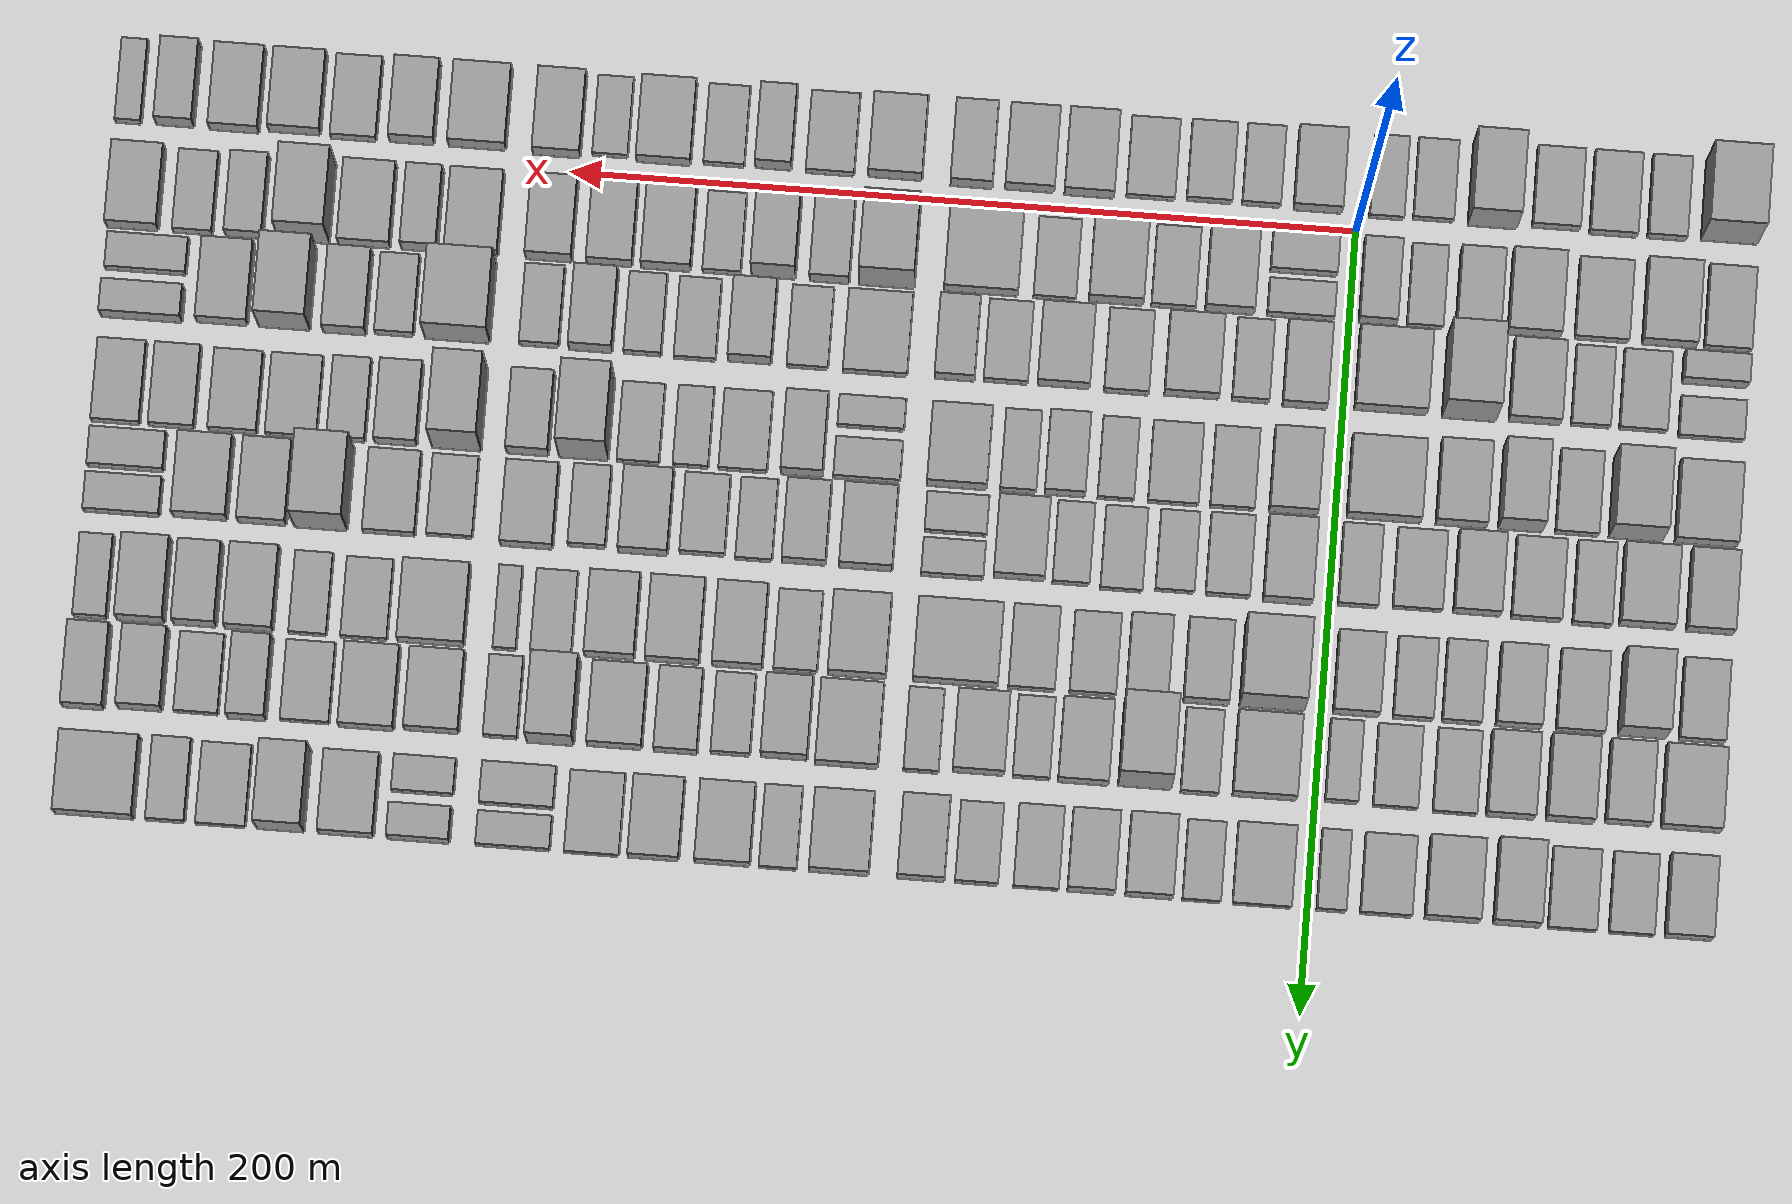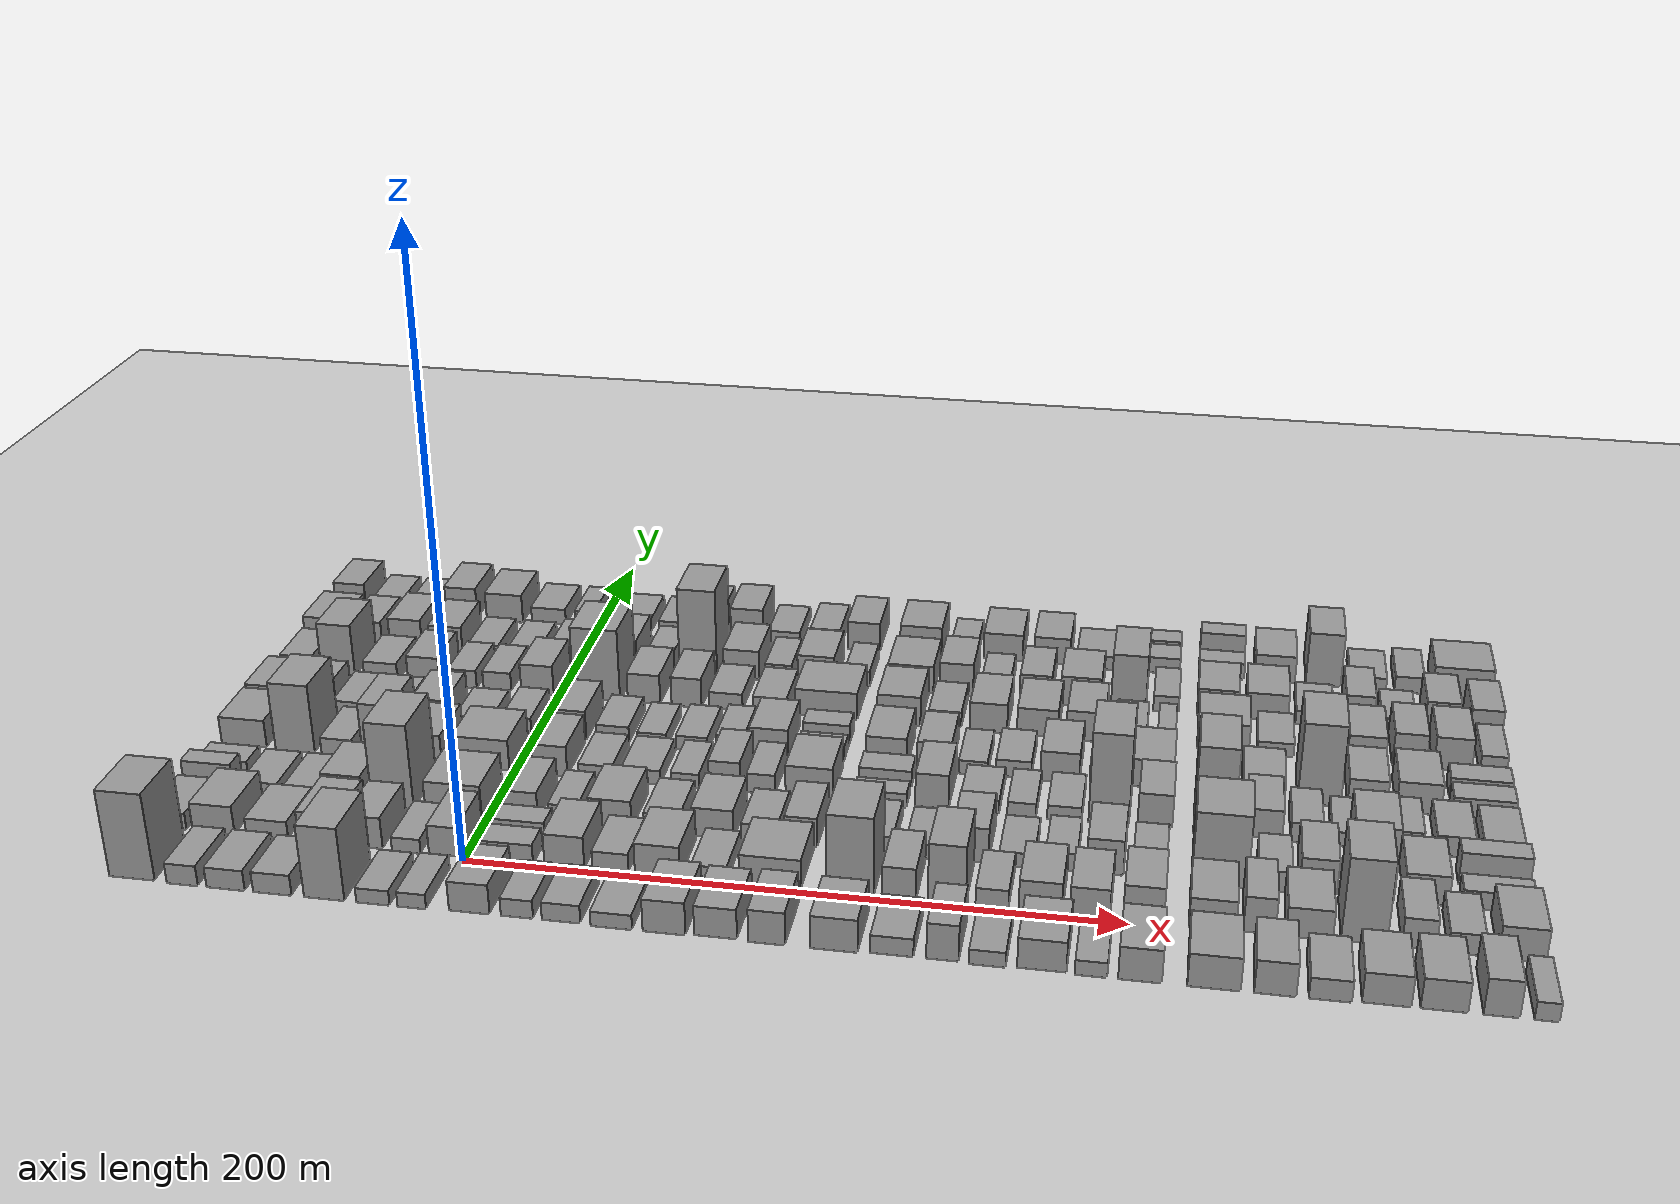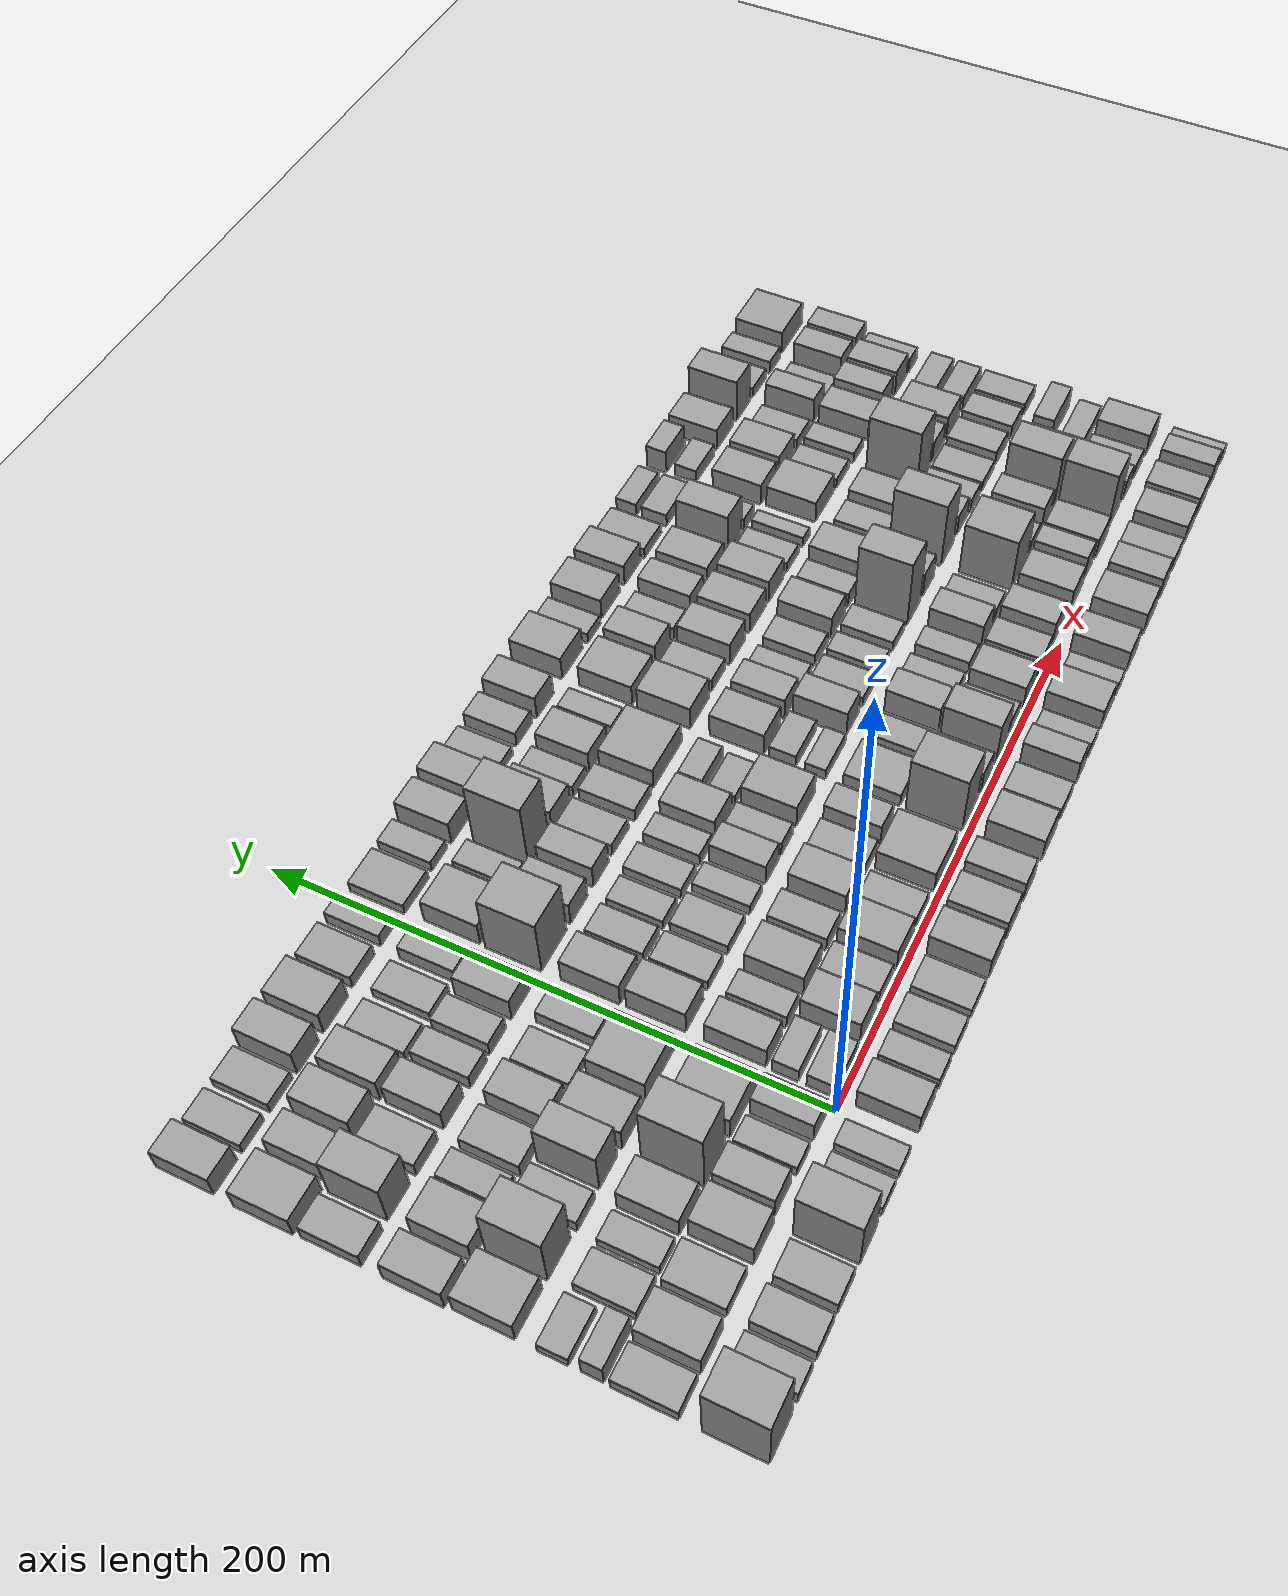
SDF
<sdf version="1.4">
 <world name="default">
  <physics type="ode">
   <max_step_size>0.01</max_step_size>
   <real_time_factor>1</real_time_factor>
   <real_time_update_rate>100</real_time_update_rate>
   <gravity>0 0 -9.8</gravity>
  </physics>
  <scene><ambient>0.4 0.4 0.4 1</ambient><background>0.7 0.7 0.7 1</background><shadows>1</shadows></scene>
  <light name="sun" type="directional">
   <diffuse>0.8 0.8 0.8 1</diffuse>
   <specular>0.2 0.2 0.2 1</specular>
   <direction>-0.5 0.1 -0.9</direction>
   <attenuation>
    <range>1000</range>
    <constant>0.9</constant>
    <linear>0.01</linear>
    <quadratic>0.001</quadratic>
   </attenuation>
  </light>
  <model name="ground_plane">
   <static>1</static>
   <pose>100 65 0 0 -0 0</pose>
   <link name="link">
    <velocity_decay><linear>0</linear><angular>0</angular></velocity_decay>
    <collision name="collision">
     <geometry><plane><normal>0 0 1</normal><size>400 250</size></plane></geometry>
     <surface><friction><ode><mu>100</mu><mu2>50</mu2></ode></friction></surface>
    </collision>
    <visual name="visual">
     <geometry><plane><normal>0 0 1</normal><size>400 250</size></plane></geometry>
     <material>
      <script><name>Gazebo/Grey</name><uri>file://media/materials/scripts/gazebo.material</uri></script>
     </material>
    </visual>
   </link>
  </model>
  <model name="box_100">
   <static>1</static>
   <pose>-94.3 -14.9 15 0 -0 0</pose>
   <link name="link">
    <velocity_decay><linear>0</linear><angular>0</angular></velocity_decay>
    <collision name="collision"><geometry><box><size>14.4 20.2 30</size></box></geometry></collision>
    <visual name="visual">
     <geometry><box><size>14.4 20.2 30</size></box></geometry>
     <material>
      <script><name>Gazebo/Grey</name><uri>file://media/materials/scripts/gazebo.material</uri></script>
     </material>
    </visual>
   </link>
  </model>
  <model name="box_200">
   <static>1</static>
   <pose>-78.44 -14.7 3 0 -0 0</pose>
   <link name="link">
    <velocity_decay><linear>0</linear><angular>0</angular></velocity_decay>
    <collision name="collision"><geometry><box><size>9.8 20.6 7</size></box></geometry></collision>
    <visual name="visual">
     <geometry><box><size>9.8 20.6 7</size></box></geometry>
     <material>
      <script><name>Gazebo/Grey</name><uri>file://media/materials/scripts/gazebo.material</uri></script>
     </material>
    </visual>
   </link>
  </model>
  <model name="box_300">
   <static>1</static>
   <pose>-64.82 -14.65 3 0 -0 0</pose>
   <link name="link">
    <velocity_decay><linear>0</linear><angular>0</angular></velocity_decay>
    <collision name="collision"><geometry><box><size>12 20.7 7</size></box></geometry></collision>
    <visual name="visual">
     <geometry><box><size>12 20.7 7</size></box></geometry>
     <material>
      <script><name>Gazebo/Grey</name><uri>file://media/materials/scripts/gazebo.material</uri></script>
     </material>
    </visual>
   </link>
  </model>
  <model name="box_400">
   <static>1</static>
   <pose>-50.24 -14.95 3 0 -0 0</pose>
   <link name="link">
    <velocity_decay><linear>0</linear><angular>0</angular></velocity_decay>
    <collision name="collision"><geometry><box><size>12 20.1 7</size></box></geometry></collision>
    <visual name="visual">
     <geometry><box><size>12 20.1 7</size></box></geometry>
     <material>
      <script><name>Gazebo/Grey</name><uri>file://media/materials/scripts/gazebo.material</uri></script>
     </material>
    </visual>
   </link>
  </model>
  <model name="box_500">
   <static>1</static>
   <pose>-34.15 -14.55 12 0 -0 0</pose>
   <link name="link">
    <velocity_decay><linear>0</linear><angular>0</angular></velocity_decay>
    <collision name="collision"><geometry><box><size>12.5 20.9 25</size></box></geometry></collision>
    <visual name="visual">
     <geometry><box><size>12.5 20.9 25</size></box></geometry>
     <material>
      <script><name>Gazebo/Grey</name><uri>file://media/materials/scripts/gazebo.material</uri></script>
     </material>
    </visual>
   </link>
  </model>
  <model name="box_600">
   <static>1</static>
   <pose>-19.13 -14.8 2 0 -0 0</pose>
   <link name="link">
    <velocity_decay><linear>0</linear><angular>0</angular></velocity_decay>
    <collision name="collision"><geometry><box><size>10.2 20.4 5</size></box></geometry></collision>
    <visual name="visual">
     <geometry><box><size>10.2 20.4 5</size></box></geometry>
     <material>
      <script><name>Gazebo/Grey</name><uri>file://media/materials/scripts/gazebo.material</uri></script>
     </material>
    </visual>
   </link>
  </model>
  <model name="box_700">
   <static>1</static>
   <pose>-7.265 -14.6 2 0 -0 0</pose>
   <link name="link">
    <velocity_decay><linear>0</linear><angular>0</angular></velocity_decay>
    <collision name="collision"><geometry><box><size>8.73 20.8 5</size></box></geometry></collision>
    <visual name="visual">
     <geometry><box><size>8.73 20.8 5</size></box></geometry>
     <material>
      <script><name>Gazebo/Grey</name><uri>file://media/materials/scripts/gazebo.material</uri></script>
     </material>
    </visual>
   </link>
  </model>
  <model name="box_110">
   <static>1</static>
   <pose>-95.6 12.5 3 0 -0 0</pose>
   <link name="link">
    <velocity_decay><linear>0</linear><angular>0</angular></velocity_decay>
    <collision name="collision"><geometry><box><size>11.8 21 6</size></box></geometry></collision>
    <visual name="visual">
     <geometry><box><size>11.8 21 6</size></box></geometry>
     <material>
      <script><name>Gazebo/Grey</name><uri>file://media/materials/scripts/gazebo.material</uri></script>
     </material>
    </visual>
   </link>
  </model>
  <model name="box_210">
   <static>1</static>
   <pose>-80.82 12.5 5 0 -0 0</pose>
   <link name="link">
    <velocity_decay><linear>0</linear><angular>0</angular></velocity_decay>
    <collision name="collision"><geometry><box><size>13.7 21 10</size></box></geometry></collision>
    <visual name="visual">
     <geometry><box><size>13.7 21 10</size></box></geometry>
     <material>
      <script><name>Gazebo/Grey</name><uri>file://media/materials/scripts/gazebo.material</uri></script>
     </material>
    </visual>
   </link>
  </model>
  <model name="box_310">
   <static>1</static>
   <pose>-63.67 12.8 3 0 -0 0</pose>
   <link name="link">
    <velocity_decay><linear>0</linear><angular>0</angular></velocity_decay>
    <collision name="collision"><geometry><box><size>13.6 20.4 6</size></box></geometry></collision>
    <visual name="visual">
     <geometry><box><size>13.6 20.4 6</size></box></geometry>
     <material>
      <script><name>Gazebo/Grey</name><uri>file://media/materials/scripts/gazebo.material</uri></script>
     </material>
    </visual>
   </link>
  </model>
  <model name="box_410">
   <static>1</static>
   <pose>-46.56 12.6 5 0 -0 0</pose>
   <link name="link">
    <velocity_decay><linear>0</linear><angular>0</angular></velocity_decay>
    <collision name="collision"><geometry><box><size>13.4 20.8 11</size></box></geometry></collision>
    <visual name="visual">
     <geometry><box><size>13.4 20.8 11</size></box></geometry>
     <material>
      <script><name>Gazebo/Grey</name><uri>file://media/materials/scripts/gazebo.material</uri></script>
     </material>
    </visual>
   </link>
  </model>
  <model name="box_510">
   <static>1</static>
   <pose>-32.19 12.9 5 0 -0 0</pose>
   <link name="link">
    <velocity_decay><linear>0</linear><angular>0</angular></velocity_decay>
    <collision name="collision"><geometry><box><size>11.1 20.2 11</size></box></geometry></collision>
    <visual name="visual">
     <geometry><box><size>11.1 20.2 11</size></box></geometry>
     <material>
      <script><name>Gazebo/Grey</name><uri>file://media/materials/scripts/gazebo.material</uri></script>
     </material>
    </visual>
   </link>
  </model>
  <model name="box_610">
   <static>1</static>
   <pose>-18.9 12.6 2 0 -0 0</pose>
   <link name="link">
    <velocity_decay><linear>0</linear><angular>0</angular></velocity_decay>
    <collision name="collision"><geometry><box><size>9.1 20.8 5</size></box></geometry></collision>
    <visual name="visual">
     <geometry><box><size>9.1 20.8 5</size></box></geometry>
     <material>
      <script><name>Gazebo/Grey</name><uri>file://media/materials/scripts/gazebo.material</uri></script>
     </material>
    </visual>
   </link>
  </model>
  <model name="box_710">
   <static>1</static>
   <pose>-6.88 12.6 5 0 -0 0</pose>
   <link name="link">
    <velocity_decay><linear>0</linear><angular>0</angular></velocity_decay>
    <collision name="collision"><geometry><box><size>9.56 20.8 10</size></box></geometry></collision>
    <visual name="visual">
     <geometry><box><size>9.56 20.8 10</size></box></geometry>
     <material>
      <script><name>Gazebo/Grey</name><uri>file://media/materials/scripts/gazebo.material</uri></script>
     </material>
    </visual>
   </link>
  </model>
  <model name="box_120">
   <static>1</static>
   <pose>-92.95 28.6 5 0 -0 0</pose>
   <link name="link">
    <velocity_decay><linear>0</linear><angular>0</angular></velocity_decay>
    <collision name="collision"><geometry><box><size>16.5 7.2 10</size></box></geometry></collision>
    <visual name="visual">
     <geometry><box><size>16.5 7.2 10</size></box></geometry>
     <material>
      <script><name>Gazebo/Grey</name><uri>file://media/materials/scripts/gazebo.material</uri></script>
     </material>
    </visual>
   </link>
  </model>
  <model name="box_1202">
   <static>1</static>
   <pose>-92.95 41 2 0 -0 0</pose>
   <link name="link">
    <velocity_decay><linear>0</linear><angular>0</angular></velocity_decay>
    <collision name="collision"><geometry><box><size>16.5 10 5</size></box></geometry></collision>
    <visual name="visual">
     <geometry><box><size>16.5 10 5</size></box></geometry>
     <material>
      <script><name>Gazebo/Grey</name><uri>file://media/materials/scripts/gazebo.material</uri></script>
     </material>
    </visual>
   </link>
  </model>
  <model name="box_220">
   <static>1</static>
   <pose>-75.71 35.05 2 0 -0 0</pose>
   <link name="link">
    <velocity_decay><linear>0</linear><angular>0</angular></velocity_decay>
    <collision name="collision"><geometry><box><size>12 20.1 5</size></box></geometry></collision>
    <visual name="visual">
     <geometry><box><size>12 20.1 5</size></box></geometry>
     <material>
      <script><name>Gazebo/Grey</name><uri>file://media/materials/scripts/gazebo.material</uri></script>
     </material>
    </visual>
   </link>
  </model>
  <model name="box_320">
   <static>1</static>
   <pose>-62.4 35.05 2 0 -0 0</pose>
   <link name="link">
    <velocity_decay><linear>0</linear><angular>0</angular></velocity_decay>
    <collision name="collision"><geometry><box><size>9.8 20.1 5</size></box></geometry></collision>
    <visual name="visual">
     <geometry><box><size>9.8 20.1 5</size></box></geometry>
     <material>
      <script><name>Gazebo/Grey</name><uri>file://media/materials/scripts/gazebo.material</uri></script>
     </material>
    </visual>
   </link>
  </model>
  <model name="box_420">
   <static>1</static>
   <pose>-48.21 35.15 5 0 -0 0</pose>
   <link name="link">
    <velocity_decay><linear>0</linear><angular>0</angular></velocity_decay>
    <collision name="collision"><geometry><box><size>13.1 20.3 10</size></box></geometry></collision>
    <visual name="visual">
     <geometry><box><size>13.1 20.3 10</size></box></geometry>
     <material>
      <script><name>Gazebo/Grey</name><uri>file://media/materials/scripts/gazebo.material</uri></script>
     </material>
    </visual>
   </link>
  </model>
  <model name="box_520">
   <static>1</static>
   <pose>-31.63 35.35 15 0 -0 0</pose>
   <link name="link">
    <velocity_decay><linear>0</linear><angular>0</angular></velocity_decay>
    <collision name="collision"><geometry><box><size>13.7 20.7 30</size></box></geometry></collision>
    <visual name="visual">
     <geometry><box><size>13.7 20.7 30</size></box></geometry>
     <material>
      <script><name>Gazebo/Grey</name><uri>file://media/materials/scripts/gazebo.material</uri></script>
     </material>
    </visual>
   </link>
  </model>
  <model name="box_620">
   <static>1</static>
   <pose>-11.78 35.15 5 0 -0 0</pose>
   <link name="link">
    <velocity_decay><linear>0</linear><angular>0</angular></velocity_decay>
    <collision name="collision"><geometry><box><size>18.36 20.3 11</size></box></geometry></collision>
    <visual name="visual">
     <geometry><box><size>18.36 20.3 11</size></box></geometry>
     <material>
      <script><name>Gazebo/Grey</name><uri>file://media/materials/scripts/gazebo.material</uri></script>
     </material>
    </visual>
   </link>
  </model>
  <model name="box_130">
   <static>1</static>
   <pose>-93.35 62.9 5 0 -0 0</pose>
   <link name="link">
    <velocity_decay><linear>0</linear><angular>0</angular></velocity_decay>
    <collision name="collision"><geometry><box><size>15.7 20.2 10</size></box></geometry></collision>
    <visual name="visual">
     <geometry><box><size>15.7 20.2 10</size></box></geometry>
     <material>
      <script><name>Gazebo/Grey</name><uri>file://media/materials/scripts/gazebo.material</uri></script>
     </material>
    </visual>
   </link>
  </model>
  <model name="box_230">
   <static>1</static>
   <pose>-75.67 62.9 12 0 -0 0</pose>
   <link name="link">
    <velocity_decay><linear>0</linear><angular>0</angular></velocity_decay>
    <collision name="collision"><geometry><box><size>13.6 20.2 25</size></box></geometry></collision>
    <visual name="visual">
     <geometry><box><size>13.6 20.2 25</size></box></geometry>
     <material>
      <script><name>Gazebo/Grey</name><uri>file://media/materials/scripts/gazebo.material</uri></script>
     </material>
    </visual>
   </link>
  </model>
  <model name="box_330">
   <static>1</static>
   <pose>-60.77 62.5 3 0 -0 0</pose>
   <link name="link">
    <velocity_decay><linear>0</linear><angular>0</angular></velocity_decay>
    <collision name="collision"><geometry><box><size>10.8 21 6</size></box></geometry></collision>
    <visual name="visual">
     <geometry><box><size>10.8 21 6</size></box></geometry>
     <material>
      <script><name>Gazebo/Grey</name><uri>file://media/materials/scripts/gazebo.material</uri></script>
     </material>
    </visual>
   </link>
  </model>
  <model name="box_430">
   <static>1</static>
   <pose>-46.5 62.65 10 0 -0 0</pose>
   <link name="link">
    <velocity_decay><linear>0</linear><angular>0</angular></velocity_decay>
    <collision name="collision"><geometry><box><size>11.2 20.7 20</size></box></geometry></collision>
    <visual name="visual">
     <geometry><box><size>11.2 20.7 20</size></box></geometry>
     <material>
      <script><name>Gazebo/Grey</name><uri>file://media/materials/scripts/gazebo.material</uri></script>
     </material>
    </visual>
   </link>
  </model>
  <model name="box_530">
   <static>1</static>
   <pose>-31.51 62.6 5 0 -0 0</pose>
   <link name="link">
    <velocity_decay><linear>0</linear><angular>0</angular></velocity_decay>
    <collision name="collision"><geometry><box><size>12.8 20.8 11</size></box></geometry></collision>
    <visual name="visual">
     <geometry><box><size>12.8 20.8 11</size></box></geometry>
     <material>
      <script><name>Gazebo/Grey</name><uri>file://media/materials/scripts/gazebo.material</uri></script>
     </material>
    </visual>
   </link>
  </model>
  <model name="box_630">
   <static>1</static>
   <pose>-11.965 62.95 5 0 -0 0</pose>
   <link name="link">
    <velocity_decay><linear>0</linear><angular>0</angular></velocity_decay>
    <collision name="collision"><geometry><box><size>18.73 20.1 11</size></box></geometry></collision>
    <visual name="visual">
     <geometry><box><size>18.73 20.1 11</size></box></geometry>
     <material>
      <script><name>Gazebo/Grey</name><uri>file://media/materials/scripts/gazebo.material</uri></script>
     </material>
    </visual>
   </link>
  </model>
  <model name="box_140">
   <static>1</static>
   <pose>-95.85 85.15 5 0 -0 0</pose>
   <link name="link">
    <velocity_decay><linear>0</linear><angular>0</angular></velocity_decay>
    <collision name="collision"><geometry><box><size>11.9 20.3 10</size></box></geometry></collision>
    <visual name="visual">
     <geometry><box><size>11.9 20.3 10</size></box></geometry>
     <material>
      <script><name>Gazebo/Grey</name><uri>file://media/materials/scripts/gazebo.material</uri></script>
     </material>
    </visual>
   </link>
  </model>
  <model name="box_240">
   <static>1</static>
   <pose>-79.9 85.05 5 0 -0 0</pose>
   <link name="link">
    <velocity_decay><linear>0</linear><angular>0</angular></velocity_decay>
    <collision name="collision"><geometry><box><size>13.8 20.1 11</size></box></geometry></collision>
    <visual name="visual">
     <geometry><box><size>13.8 20.1 11</size></box></geometry>
     <material>
      <script><name>Gazebo/Grey</name><uri>file://media/materials/scripts/gazebo.material</uri></script>
     </material>
    </visual>
   </link>
  </model>
  <model name="box_340">
   <static>1</static>
   <pose>-66.06 85.4 3 0 -0 0</pose>
   <link name="link">
    <velocity_decay><linear>0</linear><angular>0</angular></velocity_decay>
    <collision name="collision"><geometry><box><size>9.7 20.8 7</size></box></geometry></collision>
    <visual name="visual">
     <geometry><box><size>9.7 20.8 7</size></box></geometry>
     <material>
      <script><name>Gazebo/Grey</name><uri>file://media/materials/scripts/gazebo.material</uri></script>
     </material>
    </visual>
   </link>
  </model>
  <model name="box_440">
   <static>1</static>
   <pose>-52.05 85.2 3 0 -0 0</pose>
   <link name="link">
    <velocity_decay><linear>0</linear><angular>0</angular></velocity_decay>
    <collision name="collision"><geometry><box><size>12.6 20.4 7</size></box></geometry></collision>
    <visual name="visual">
     <geometry><box><size>12.6 20.4 7</size></box></geometry>
     <material>
      <script><name>Gazebo/Grey</name><uri>file://media/materials/scripts/gazebo.material</uri></script>
     </material>
    </visual>
   </link>
  </model>
  <model name="box_540">
   <static>1</static>
   <pose>-37.03 85.1 5 0 -0 0</pose>
   <link name="link">
    <velocity_decay><linear>0</linear><angular>0</angular></velocity_decay>
    <collision name="collision"><geometry><box><size>11.9 20.2 10</size></box></geometry></collision>
    <visual name="visual">
     <geometry><box><size>11.9 20.2 10</size></box></geometry>
     <material>
      <script><name>Gazebo/Grey</name><uri>file://media/materials/scripts/gazebo.material</uri></script>
     </material>
    </visual>
   </link>
  </model>
  <model name="box_640">
   <static>1</static>
   <pose>-22.04 85.05 2 0 -0 0</pose>
   <link name="link">
    <velocity_decay><linear>0</linear><angular>0</angular></velocity_decay>
    <collision name="collision"><geometry><box><size>12.5 20.1 5</size></box></geometry></collision>
    <visual name="visual">
     <geometry><box><size>12.5 20.1 5</size></box></geometry>
     <material>
      <script><name>Gazebo/Grey</name><uri>file://media/materials/scripts/gazebo.material</uri></script>
     </material>
    </visual>
   </link>
  </model>
  <model name="box_740">
   <static>1</static>
   <pose>-6.99001 85.25 3 0 -0 0</pose>
   <link name="link">
    <velocity_decay><linear>0</linear><angular>0</angular></velocity_decay>
    <collision name="collision"><geometry><box><size>9.98001 20.5 6</size></box></geometry></collision>
    <visual name="visual">
     <geometry><box><size>9.98001 20.5 6</size></box></geometry>
     <material>
      <script><name>Gazebo/Grey</name><uri>file://media/materials/scripts/gazebo.material</uri></script>
     </material>
    </visual>
   </link>
  </model>
  <model name="box_150">
   <static>1</static>
   <pose>-95.65 112.8 3 0 -0 0</pose>
   <link name="link">
    <velocity_decay><linear>0</linear><angular>0</angular></velocity_decay>
    <collision name="collision"><geometry><box><size>11.5 20.4 7</size></box></geometry></collision>
    <visual name="visual">
     <geometry><box><size>11.5 20.4 7</size></box></geometry>
     <material>
      <script><name>Gazebo/Grey</name><uri>file://media/materials/scripts/gazebo.material</uri></script>
     </material>
    </visual>
   </link>
  </model>
  <model name="box_250">
   <static>1</static>
   <pose>-80.57 112.9 10 0 -0 0</pose>
   <link name="link">
    <velocity_decay><linear>0</linear><angular>0</angular></velocity_decay>
    <collision name="collision"><geometry><box><size>12.2 20.2 20</size></box></geometry></collision>
    <visual name="visual">
     <geometry><box><size>12.2 20.2 20</size></box></geometry>
     <material>
      <script><name>Gazebo/Grey</name><uri>file://media/materials/scripts/gazebo.material</uri></script>
     </material>
    </visual>
   </link>
  </model>
  <model name="box_350">
   <static>1</static>
   <pose>-65.01 112.85 3 0 -0 0</pose>
   <link name="link">
    <velocity_decay><linear>0</linear><angular>0</angular></velocity_decay>
    <collision name="collision"><geometry><box><size>12.2 20.3 7</size></box></geometry></collision>
    <visual name="visual">
     <geometry><box><size>12.2 20.3 7</size></box></geometry>
     <material>
      <script><name>Gazebo/Grey</name><uri>file://media/materials/scripts/gazebo.material</uri></script>
     </material>
    </visual>
   </link>
  </model>
  <model name="box_450">
   <static>1</static>
   <pose>-49.37 112.9 5 0 -0 0</pose>
   <link name="link">
    <velocity_decay><linear>0</linear><angular>0</angular></velocity_decay>
    <collision name="collision"><geometry><box><size>11.4 20.2 10</size></box></geometry></collision>
    <visual name="visual">
     <geometry><box><size>11.4 20.2 10</size></box></geometry>
     <material>
      <script><name>Gazebo/Grey</name><uri>file://media/materials/scripts/gazebo.material</uri></script>
     </material>
    </visual>
   </link>
  </model>
  <model name="box_550">
   <static>1</static>
   <pose>-35.08 112.75 3 0 -0 0</pose>
   <link name="link">
    <velocity_decay><linear>0</linear><angular>0</angular></velocity_decay>
    <collision name="collision"><geometry><box><size>9.8 20.5 7</size></box></geometry></collision>
    <visual name="visual">
     <geometry><box><size>9.8 20.5 7</size></box></geometry>
     <material>
      <script><name>Gazebo/Grey</name><uri>file://media/materials/scripts/gazebo.material</uri></script>
     </material>
    </visual>
   </link>
  </model>
  <model name="box_650">
   <static>1</static>
   <pose>-22.82 112.9 3 0 -0 0</pose>
   <link name="link">
    <velocity_decay><linear>0</linear><angular>0</angular></velocity_decay>
    <collision name="collision"><geometry><box><size>10 20.2 7</size></box></geometry></collision>
    <visual name="visual">
     <geometry><box><size>10 20.2 7</size></box></geometry>
     <material>
      <script><name>Gazebo/Grey</name><uri>file://media/materials/scripts/gazebo.material</uri></script>
     </material>
    </visual>
   </link>
  </model>
  <model name="box_750">
   <static>1</static>
   <pose>-8.495 112.9 5 0 -0 0</pose>
   <link name="link">
    <velocity_decay><linear>0</linear><angular>0</angular></velocity_decay>
    <collision name="collision"><geometry><box><size>11.59 20.2 11</size></box></geometry></collision>
    <visual name="visual">
     <geometry><box><size>11.59 20.2 11</size></box></geometry>
     <material>
      <script><name>Gazebo/Grey</name><uri>file://media/materials/scripts/gazebo.material</uri></script>
     </material>
    </visual>
   </link>
  </model>
  <model name="box_160">
   <static>1</static>
   <pose>-94.35 135.3 5 0 -0 0</pose>
   <link name="link">
    <velocity_decay><linear>0</linear><angular>0</angular></velocity_decay>
    <collision name="collision"><geometry><box><size>15.1 20.6 10</size></box></geometry></collision>
    <visual name="visual">
     <geometry><box><size>15.1 20.6 10</size></box></geometry>
     <material>
      <script><name>Gazebo/Grey</name><uri>file://media/materials/scripts/gazebo.material</uri></script>
     </material>
    </visual>
   </link>
  </model>
  <model name="box_260">
   <static>1</static>
   <pose>-78.43 135.2 5 0 -0 0</pose>
   <link name="link">
    <velocity_decay><linear>0</linear><angular>0</angular></velocity_decay>
    <collision name="collision"><geometry><box><size>11.3 20.4 10</size></box></geometry></collision>
    <visual name="visual">
     <geometry><box><size>11.3 20.4 10</size></box></geometry>
     <material>
      <script><name>Gazebo/Grey</name><uri>file://media/materials/scripts/gazebo.material</uri></script>
     </material>
    </visual>
   </link>
  </model>
  <model name="box_360">
   <static>1</static>
   <pose>-63.87 135.45 6 0 -0 0</pose>
   <link name="link">
    <velocity_decay><linear>0</linear><angular>0</angular></velocity_decay>
    <collision name="collision"><geometry><box><size>12 20.9 12</size></box></geometry></collision>
    <visual name="visual">
     <geometry><box><size>12 20.9 12</size></box></geometry>
     <material>
      <script><name>Gazebo/Grey</name><uri>file://media/materials/scripts/gazebo.material</uri></script>
     </material>
    </visual>
   </link>
  </model>
  <model name="box_460">
   <static>1</static>
   <pose>-48.93 135.45 5 0 -0 0</pose>
   <link name="link">
    <velocity_decay><linear>0</linear><angular>0</angular></velocity_decay>
    <collision name="collision"><geometry><box><size>12.1 20.9 11</size></box></geometry></collision>
    <visual name="visual">
     <geometry><box><size>12.1 20.9 11</size></box></geometry>
     <material>
      <script><name>Gazebo/Grey</name><uri>file://media/materials/scripts/gazebo.material</uri></script>
     </material>
    </visual>
   </link>
  </model>
  <model name="box_560">
   <static>1</static>
   <pose>-34.96 135.5 2 0 -0 0</pose>
   <link name="link">
    <velocity_decay><linear>0</linear><angular>0</angular></velocity_decay>
    <collision name="collision"><geometry><box><size>11 21 5</size></box></geometry></collision>
    <visual name="visual">
     <geometry><box><size>11 21 5</size></box></geometry>
     <material>
      <script><name>Gazebo/Grey</name><uri>file://media/materials/scripts/gazebo.material</uri></script>
     </material>
    </visual>
   </link>
  </model>
  <model name="box_660">
   <static>1</static>
   <pose>-19.97 135.35 2 0 -0 0</pose>
   <link name="link">
    <velocity_decay><linear>0</linear><angular>0</angular></velocity_decay>
    <collision name="collision"><geometry><box><size>11.2 20.7 5</size></box></geometry></collision>
    <visual name="visual">
     <geometry><box><size>11.2 20.7 5</size></box></geometry>
     <material>
      <script><name>Gazebo/Grey</name><uri>file://media/materials/scripts/gazebo.material</uri></script>
     </material>
    </visual>
   </link>
  </model>
  <model name="box_760">
   <static>1</static>
   <pose>-6.4 135.2 3 0 -0 0</pose>
   <link name="link">
    <velocity_decay><linear>0</linear><angular>0</angular></velocity_decay>
    <collision name="collision"><geometry><box><size>8.19999 20.4 7</size></box></geometry></collision>
    <visual name="visual">
     <geometry><box><size>8.19999 20.4 7</size></box></geometry>
     <material>
      <script><name>Gazebo/Grey</name><uri>file://media/materials/scripts/gazebo.material</uri></script>
     </material>
    </visual>
   </link>
  </model>
  <model name="box_170">
   <static>1</static>
   <pose>-95.5 162.8 5 0 -0 0</pose>
   <link name="link">
    <velocity_decay><linear>0</linear><angular>0</angular></velocity_decay>
    <collision name="collision"><geometry><box><size>11.8 20.4 10</size></box></geometry></collision>
    <visual name="visual">
     <geometry><box><size>11.8 20.4 10</size></box></geometry>
     <material>
      <script><name>Gazebo/Grey</name><uri>file://media/materials/scripts/gazebo.material</uri></script>
     </material>
    </visual>
   </link>
  </model>
  <model name="box_270">
   <static>1</static>
   <pose>-81.22 162.85 2 0 -0 0</pose>
   <link name="link">
    <velocity_decay><linear>0</linear><angular>0</angular></velocity_decay>
    <collision name="collision"><geometry><box><size>11.3 20.3 5</size></box></geometry></collision>
    <visual name="visual">
     <geometry><box><size>11.3 20.3 5</size></box></geometry>
     <material>
      <script><name>Gazebo/Grey</name><uri>file://media/materials/scripts/gazebo.material</uri></script>
     </material>
    </visual>
   </link>
  </model>
  <model name="box_370">
   <static>1</static>
   <pose>-66.34 162.8 2 0 -0 0</pose>
   <link name="link">
    <velocity_decay><linear>0</linear><angular>0</angular></velocity_decay>
    <collision name="collision"><geometry><box><size>12.1 20.4 5</size></box></geometry></collision>
    <visual name="visual">
     <geometry><box><size>12.1 20.4 5</size></box></geometry>
     <material>
      <script><name>Gazebo/Grey</name><uri>file://media/materials/scripts/gazebo.material</uri></script>
     </material>
    </visual>
   </link>
  </model>
  <model name="box_470">
   <static>1</static>
   <pose>-52.39 162.55 6 0 -0 0</pose>
   <link name="link">
    <velocity_decay><linear>0</linear><angular>0</angular></velocity_decay>
    <collision name="collision"><geometry><box><size>11.8 20.9 12</size></box></geometry></collision>
    <visual name="visual">
     <geometry><box><size>11.8 20.9 12</size></box></geometry>
     <material>
      <script><name>Gazebo/Grey</name><uri>file://media/materials/scripts/gazebo.material</uri></script>
     </material>
    </visual>
   </link>
  </model>
  <model name="box_570">
   <static>1</static>
   <pose>-36.19 162.8 5 0 -0 0</pose>
   <link name="link">
    <velocity_decay><linear>0</linear><angular>0</angular></velocity_decay>
    <collision name="collision"><geometry><box><size>13.8 20.4 11</size></box></geometry></collision>
    <visual name="visual">
     <geometry><box><size>13.8 20.4 11</size></box></geometry>
     <material>
      <script><name>Gazebo/Grey</name><uri>file://media/materials/scripts/gazebo.material</uri></script>
     </material>
    </visual>
   </link>
  </model>
  <model name="box_670">
   <static>1</static>
   <pose>-19.51 162.95 3 0 -0 0</pose>
   <link name="link">
    <velocity_decay><linear>0</linear><angular>0</angular></velocity_decay>
    <collision name="collision"><geometry><box><size>12.9 20.1 6</size></box></geometry></collision>
    <visual name="visual">
     <geometry><box><size>12.9 20.1 6</size></box></geometry>
     <material>
      <script><name>Gazebo/Grey</name><uri>file://media/materials/scripts/gazebo.material</uri></script>
     </material>
    </visual>
   </link>
  </model>
  <model name="box_770">
   <static>1</static>
   <pose>-5.75499 162.9 3 0 -0 0</pose>
   <link name="link">
    <velocity_decay><linear>0</linear><angular>0</angular></velocity_decay>
    <collision name="collision"><geometry><box><size>7.30998 20.2 6</size></box></geometry></collision>
    <visual name="visual">
     <geometry><box><size>7.30998 20.2 6</size></box></geometry>
     <material>
      <script><name>Gazebo/Grey</name><uri>file://media/materials/scripts/gazebo.material</uri></script>
     </material>
    </visual>
   </link>
  </model>
  <model name="box_101">
   <static>1</static>
   <pose>10.25 -14.8 5 0 -0 0</pose>
   <link name="link">
    <velocity_decay><linear>0</linear><angular>0</angular></velocity_decay>
    <collision name="collision"><geometry><box><size>12.3 20.4 10</size></box></geometry></collision>
    <visual name="visual">
     <geometry><box><size>12.3 20.4 10</size></box></geometry>
     <material>
      <script><name>Gazebo/Grey</name><uri>file://media/materials/scripts/gazebo.material</uri></script>
     </material>
    </visual>
   </link>
  </model>
  <model name="box_201">
   <static>1</static>
   <pose>24.62 -14.95 3 0 -0 0</pose>
   <link name="link">
    <velocity_decay><linear>0</linear><angular>0</angular></velocity_decay>
    <collision name="collision"><geometry><box><size>9.7 20.1 6</size></box></geometry></collision>
    <visual name="visual">
     <geometry><box><size>9.7 20.1 6</size></box></geometry>
     <material>
      <script><name>Gazebo/Grey</name><uri>file://media/materials/scripts/gazebo.material</uri></script>
     </material>
    </visual>
   </link>
  </model>
  <model name="box_301">
   <static>1</static>
   <pose>37.82 -14.95 3 0 -0 0</pose>
   <link name="link">
    <velocity_decay><linear>0</linear><angular>0</angular></velocity_decay>
    <collision name="collision"><geometry><box><size>11.5 20.1 6</size></box></geometry></collision>
    <visual name="visual">
     <geometry><box><size>11.5 20.1 6</size></box></geometry>
     <material>
      <script><name>Gazebo/Grey</name><uri>file://media/materials/scripts/gazebo.material</uri></script>
     </material>
    </visual>
   </link>
  </model>
  <model name="box_401">
   <static>1</static>
   <pose>52.74 -14.85 2 0 -0 0</pose>
   <link name="link">
    <velocity_decay><linear>0</linear><angular>0</angular></velocity_decay>
    <collision name="collision"><geometry><box><size>12.3 20.3 5</size></box></geometry></collision>
    <visual name="visual">
     <geometry><box><size>12.3 20.3 5</size></box></geometry>
     <material>
      <script><name>Gazebo/Grey</name><uri>file://media/materials/scripts/gazebo.material</uri></script>
     </material>
    </visual>
   </link>
  </model>
  <model name="box_501">
   <static>1</static>
   <pose>68.31 -14.55 5 0 -0 0</pose>
   <link name="link">
    <velocity_decay><linear>0</linear><angular>0</angular></velocity_decay>
    <collision name="collision"><geometry><box><size>12.6 20.9 11</size></box></geometry></collision>
    <visual name="visual">
     <geometry><box><size>12.6 20.9 11</size></box></geometry>
     <material>
      <script><name>Gazebo/Grey</name><uri>file://media/materials/scripts/gazebo.material</uri></script>
     </material>
    </visual>
   </link>
  </model>
  <model name="box_601">
   <static>1</static>
   <pose>83.43 -14.65 5 0 -0 0</pose>
   <link name="link">
    <velocity_decay><linear>0</linear><angular>0</angular></velocity_decay>
    <collision name="collision"><geometry><box><size>12.5 20.7 10</size></box></geometry></collision>
    <visual name="visual">
     <geometry><box><size>12.5 20.7 10</size></box></geometry>
     <material>
      <script><name>Gazebo/Grey</name><uri>file://media/materials/scripts/gazebo.material</uri></script>
     </material>
    </visual>
   </link>
  </model>
  <model name="box_701">
   <static>1</static>
   <pose>98.255 -14.6 5 0 -0 0</pose>
   <link name="link">
    <velocity_decay><linear>0</linear><angular>0</angular></velocity_decay>
    <collision name="collision"><geometry><box><size>10.69 20.8 11</size></box></geometry></collision>
    <visual name="visual">
     <geometry><box><size>10.69 20.8 11</size></box></geometry>
     <material>
      <script><name>Gazebo/Grey</name><uri>file://media/materials/scripts/gazebo.material</uri></script>
     </material>
    </visual>
   </link>
  </model>
  <model name="box_111">
   <static>1</static>
   <pose>12.65 6.8 3 0 -0 0</pose>
   <link name="link">
    <velocity_decay><linear>0</linear><angular>0</angular></velocity_decay>
    <collision name="collision"><geometry><box><size>16.9 9.6 7</size></box></geometry></collision>
    <visual name="visual">
     <geometry><box><size>16.9 9.6 7</size></box></geometry>
     <material>
      <script><name>Gazebo/Grey</name><uri>file://media/materials/scripts/gazebo.material</uri></script>
     </material>
    </visual>
   </link>
  </model>
  <model name="box_1112">
   <static>1</static>
   <pose>12.65 18.6 3 0 -0 0</pose>
   <link name="link">
    <velocity_decay><linear>0</linear><angular>0</angular></velocity_decay>
    <collision name="collision"><geometry><box><size>16.9 8.8 7</size></box></geometry></collision>
    <visual name="visual">
     <geometry><box><size>16.9 8.8 7</size></box></geometry>
     <material>
      <script><name>Gazebo/Grey</name><uri>file://media/materials/scripts/gazebo.material</uri></script>
     </material>
    </visual>
   </link>
  </model>
  <model name="box_211">
   <static>1</static>
   <pose>30.63 12.85 5 0 -0 0</pose>
   <link name="link">
    <velocity_decay><linear>0</linear><angular>0</angular></velocity_decay>
    <collision name="collision"><geometry><box><size>12.4 20.3 11</size></box></geometry></collision>
    <visual name="visual">
     <geometry><box><size>12.4 20.3 11</size></box></geometry>
     <material>
      <script><name>Gazebo/Grey</name><uri>file://media/materials/scripts/gazebo.material</uri></script>
     </material>
    </visual>
   </link>
  </model>
  <model name="box_311">
   <static>1</static>
   <pose>44.92 12.85 3 0 -0 0</pose>
   <link name="link">
    <velocity_decay><linear>0</linear><angular>0</angular></velocity_decay>
    <collision name="collision"><geometry><box><size>11.2 20.3 6</size></box></geometry></collision>
    <visual name="visual">
     <geometry><box><size>11.2 20.3 6</size></box></geometry>
     <material>
      <script><name>Gazebo/Grey</name><uri>file://media/materials/scripts/gazebo.material</uri></script>
     </material>
    </visual>
   </link>
  </model>
  <model name="box_411">
   <static>1</static>
   <pose>59.4707 12.5461 5 0 -0 0</pose>
   <link name="link">
    <velocity_decay><linear>0</linear><angular>0</angular></velocity_decay>
    <collision name="collision"><geometry><box><size>13.8 20.6 11</size></box></geometry></collision>
    <visual name="visual">
     <geometry><box><size>13.8 20.6 11</size></box></geometry>
     <material>
      <script><name>Gazebo/Grey</name><uri>file://media/materials/scripts/gazebo.material</uri></script>
     </material>
    </visual>
   </link>
  </model>
  <model name="box_511">
   <static>1</static>
   <pose>75.05 12.85 2 0 -0 0</pose>
   <link name="link">
    <velocity_decay><linear>0</linear><angular>0</angular></velocity_decay>
    <collision name="collision"><geometry><box><size>10.8 20.3 5</size></box></geometry></collision>
    <visual name="visual">
     <geometry><box><size>10.8 20.3 5</size></box></geometry>
     <material>
      <script><name>Gazebo/Grey</name><uri>file://media/materials/scripts/gazebo.material</uri></script>
     </material>
    </visual>
   </link>
  </model>
  <model name="box_611">
   <static>1</static>
   <pose>93.74 12.65 5 0 -0 0</pose>
   <link name="link">
    <velocity_decay><linear>0</linear><angular>0</angular></velocity_decay>
    <collision name="collision"><geometry><box><size>18.72 20.7 10</size></box></geometry></collision>
    <visual name="visual">
     <geometry><box><size>18.72 20.7 10</size></box></geometry>
     <material>
      <script><name>Gazebo/Grey</name><uri>file://media/materials/scripts/gazebo.material</uri></script>
     </material>
    </visual>
   </link>
  </model>
  <model name="box_121">
   <static>1</static>
   <pose>10 35.45 5 0 -0 0</pose>
   <link name="link">
    <velocity_decay><linear>0</linear><angular>0</angular></velocity_decay>
    <collision name="collision"><geometry><box><size>11.2 20.9 10</size></box></geometry></collision>
    <visual name="visual">
     <geometry><box><size>11.2 20.9 10</size></box></geometry>
     <material>
      <script><name>Gazebo/Grey</name><uri>file://media/materials/scripts/gazebo.material</uri></script>
     </material>
    </visual>
   </link>
  </model>
  <model name="box_221">
   <static>1</static>
   <pose>23.73 35.2 3 0 -0 0</pose>
   <link name="link">
    <velocity_decay><linear>0</linear><angular>0</angular></velocity_decay>
    <collision name="collision"><geometry><box><size>9.3 20.4 7</size></box></geometry></collision>
    <visual name="visual">
     <geometry><box><size>9.3 20.4 7</size></box></geometry>
     <material>
      <script><name>Gazebo/Grey</name><uri>file://media/materials/scripts/gazebo.material</uri></script>
     </material>
    </visual>
   </link>
  </model>
  <model name="box_321">
   <static>1</static>
   <pose>38.66 35.2 5 0 -0 0</pose>
   <link name="link">
    <velocity_decay><linear>0</linear><angular>0</angular></velocity_decay>
    <collision name="collision"><geometry><box><size>13.8 20.4 10</size></box></geometry></collision>
    <visual name="visual">
     <geometry><box><size>13.8 20.4 10</size></box></geometry>
     <material>
      <script><name>Gazebo/Grey</name><uri>file://media/materials/scripts/gazebo.material</uri></script>
     </material>
    </visual>
   </link>
  </model>
  <model name="box_421">
   <static>1</static>
   <pose>55.17 35.35 3 0 -0 0</pose>
   <link name="link">
    <velocity_decay><linear>0</linear><angular>0</angular></velocity_decay>
    <collision name="collision"><geometry><box><size>11.3 20.7 7</size></box></geometry></collision>
    <visual name="visual">
     <geometry><box><size>11.3 20.7 7</size></box></geometry>
     <material>
      <script><name>Gazebo/Grey</name><uri>file://media/materials/scripts/gazebo.material</uri></script>
     </material>
    </visual>
   </link>
  </model>
  <model name="box_521">
   <static>1</static>
   <pose>71.13 35.15 5 0 -0 0</pose>
   <link name="link">
    <velocity_decay><linear>0</linear><angular>0</angular></velocity_decay>
    <collision name="collision"><geometry><box><size>13.2 20.3 10</size></box></geometry></collision>
    <visual name="visual">
     <geometry><box><size>13.2 20.3 10</size></box></geometry>
     <material>
      <script><name>Gazebo/Grey</name><uri>file://media/materials/scripts/gazebo.material</uri></script>
     </material>
    </visual>
   </link>
  </model>
  <model name="box_621">
   <static>1</static>
   <pose>85.77 35.2 3 0 -0 0</pose>
   <link name="link">
    <velocity_decay><linear>0</linear><angular>0</angular></velocity_decay>
    <collision name="collision"><geometry><box><size>11.2 20.4 6</size></box></geometry></collision>
    <visual name="visual">
     <geometry><box><size>11.2 20.4 6</size></box></geometry>
     <material>
      <script><name>Gazebo/Grey</name><uri>file://media/materials/scripts/gazebo.material</uri></script>
     </material>
    </visual>
   </link>
  </model>
  <model name="box_721">
   <static>1</static>
   <pose>98.725 35.3 5 0 -0 0</pose>
   <link name="link">
    <velocity_decay><linear>0</linear><angular>0</angular></velocity_decay>
    <collision name="collision"><geometry><box><size>10.15 20.6 10</size></box></geometry></collision>
    <visual name="visual">
     <geometry><box><size>10.15 20.6 10</size></box></geometry>
     <material>
      <script><name>Gazebo/Grey</name><uri>file://media/materials/scripts/gazebo.material</uri></script>
     </material>
    </visual>
   </link>
  </model>
  <model name="box_131">
   <static>1</static>
   <pose>10.9 62.65 5 0 -0 0</pose>
   <link name="link">
    <velocity_decay><linear>0</linear><angular>0</angular></velocity_decay>
    <collision name="collision"><geometry><box><size>12.2 20.7 11</size></box></geometry></collision>
    <visual name="visual">
     <geometry><box><size>12.2 20.7 11</size></box></geometry>
     <material>
      <script><name>Gazebo/Grey</name><uri>file://media/materials/scripts/gazebo.material</uri></script>
     </material>
    </visual>
   </link>
  </model>
  <model name="box_231">
   <static>1</static>
   <pose>26.34 62.8 2 0 -0 0</pose>
   <link name="link">
    <velocity_decay><linear>0</linear><angular>0</angular></velocity_decay>
    <collision name="collision"><geometry><box><size>11.2 20.4 5</size></box></geometry></collision>
    <visual name="visual">
     <geometry><box><size>11.2 20.4 5</size></box></geometry>
     <material>
      <script><name>Gazebo/Grey</name><uri>file://media/materials/scripts/gazebo.material</uri></script>
     </material>
    </visual>
   </link>
  </model>
  <model name="box_331">
   <static>1</static>
   <pose>41.33 62.75 2 0 -0 0</pose>
   <link name="link">
    <velocity_decay><linear>0</linear><angular>0</angular></velocity_decay>
    <collision name="collision"><geometry><box><size>12.7 20.5 5</size></box></geometry></collision>
    <visual name="visual">
     <geometry><box><size>12.7 20.5 5</size></box></geometry>
     <material>
      <script><name>Gazebo/Grey</name><uri>file://media/materials/scripts/gazebo.material</uri></script>
     </material>
    </visual>
   </link>
  </model>
  <model name="box_431">
   <static>1</static>
   <pose>55.84 62.7 2 0 -0 0</pose>
   <link name="link">
    <velocity_decay><linear>0</linear><angular>0</angular></velocity_decay>
    <collision name="collision"><geometry><box><size>9.2 20.6 5</size></box></geometry></collision>
    <visual name="visual">
     <geometry><box><size>9.2 20.6 5</size></box></geometry>
     <material>
      <script><name>Gazebo/Grey</name><uri>file://media/materials/scripts/gazebo.material</uri></script>
     </material>
    </visual>
   </link>
  </model>
  <model name="box_531">
   <static>1</static>
   <pose>68.73 62.8 5 0 -0 0</pose>
   <link name="link">
    <velocity_decay><linear>0</linear><angular>0</angular></velocity_decay>
    <collision name="collision"><geometry><box><size>10.2 20.4 10</size></box></geometry></collision>
    <visual name="visual">
     <geometry><box><size>10.2 20.4 10</size></box></geometry>
     <material>
      <script><name>Gazebo/Grey</name><uri>file://media/materials/scripts/gazebo.material</uri></script>
     </material>
    </visual>
   </link>
  </model>
  <model name="box_631">
   <static>1</static>
   <pose>80.54 62.85 3 0 -0 0</pose>
   <link name="link">
    <velocity_decay><linear>0</linear><angular>0</angular></velocity_decay>
    <collision name="collision"><geometry><box><size>9.1 20.3 7</size></box></geometry></collision>
    <visual name="visual">
     <geometry><box><size>9.1 20.3 7</size></box></geometry>
     <material>
      <script><name>Gazebo/Grey</name><uri>file://media/materials/scripts/gazebo.material</uri></script>
     </material>
    </visual>
   </link>
  </model>
  <model name="box_731">
   <static>1</static>
   <pose>96.02 62.95 5 0 -0 0</pose>
   <link name="link">
    <velocity_decay><linear>0</linear><angular>0</angular></velocity_decay>
    <collision name="collision"><geometry><box><size>15.16 20.1 11</size></box></geometry></collision>
    <visual name="visual">
     <geometry><box><size>15.16 20.1 11</size></box></geometry>
     <material>
      <script><name>Gazebo/Grey</name><uri>file://media/materials/scripts/gazebo.material</uri></script>
     </material>
    </visual>
   </link>
  </model>
  <model name="box_141">
   <static>1</static>
   <pose>10.75 85.45 5 0 -0 0</pose>
   <link name="link">
    <velocity_decay><linear>0</linear><angular>0</angular></velocity_decay>
    <collision name="collision"><geometry><box><size>12.3 20.9 11</size></box></geometry></collision>
    <visual name="visual">
     <geometry><box><size>12.3 20.9 11</size></box></geometry>
     <material>
      <script><name>Gazebo/Grey</name><uri>file://media/materials/scripts/gazebo.material</uri></script>
     </material>
    </visual>
   </link>
  </model>
  <model name="box_241">
   <static>1</static>
   <pose>25.92 85.25 3 0 -0 0</pose>
   <link name="link">
    <velocity_decay><linear>0</linear><angular>0</angular></velocity_decay>
    <collision name="collision"><geometry><box><size>11.1 20.5 6</size></box></geometry></collision>
    <visual name="visual">
     <geometry><box><size>11.1 20.5 6</size></box></geometry>
     <material>
      <script><name>Gazebo/Grey</name><uri>file://media/materials/scripts/gazebo.material</uri></script>
     </material>
    </visual>
   </link>
  </model>
  <model name="box_341">
   <static>1</static>
   <pose>39.24 85.15 2 0 -0 0</pose>
   <link name="link">
    <velocity_decay><linear>0</linear><angular>0</angular></velocity_decay>
    <collision name="collision"><geometry><box><size>9.8 20.3 5</size></box></geometry></collision>
    <visual name="visual">
     <geometry><box><size>9.8 20.3 5</size></box></geometry>
     <material>
      <script><name>Gazebo/Grey</name><uri>file://media/materials/scripts/gazebo.material</uri></script>
     </material>
    </visual>
   </link>
  </model>
  <model name="box_441">
   <static>1</static>
   <pose>52.73 85.5 2 0 -0 0</pose>
   <link name="link">
    <velocity_decay><linear>0</linear><angular>0</angular></velocity_decay>
    <collision name="collision"><geometry><box><size>10.6 21 5</size></box></geometry></collision>
    <visual name="visual">
     <geometry><box><size>10.6 21 5</size></box></geometry>
     <material>
      <script><name>Gazebo/Grey</name><uri>file://media/materials/scripts/gazebo.material</uri></script>
     </material>
    </visual>
   </link>
  </model>
  <model name="box_541">
   <static>1</static>
   <pose>65.51 85.25 3 0 -0 0</pose>
   <link name="link">
    <velocity_decay><linear>0</linear><angular>0</angular></velocity_decay>
    <collision name="collision"><geometry><box><size>9.3 20.5 6</size></box></geometry></collision>
    <visual name="visual">
     <geometry><box><size>9.3 20.5 6</size></box></geometry>
     <material>
      <script><name>Gazebo/Grey</name><uri>file://media/materials/scripts/gazebo.material</uri></script>
     </material>
    </visual>
   </link>
  </model>
  <model name="box_641">
   <static>1</static>
   <pose>78.61 85.05 5 0 -0 0</pose>
   <link name="link">
    <velocity_decay><linear>0</linear><angular>0</angular></velocity_decay>
    <collision name="collision"><geometry><box><size>12.9 20.1 10</size></box></geometry></collision>
    <visual name="visual">
     <geometry><box><size>12.9 20.1 10</size></box></geometry>
     <material>
      <script><name>Gazebo/Grey</name><uri>file://media/materials/scripts/gazebo.material</uri></script>
     </material>
    </visual>
   </link>
  </model>
  <model name="box_741">
   <static>1</static>
   <pose>95.455 79.9 2 0 -0 0</pose>
   <link name="link">
    <velocity_decay><linear>0</linear><angular>0</angular></velocity_decay>
    <collision name="collision"><geometry><box><size>15.69 9.8 5</size></box></geometry></collision>
    <visual name="visual">
     <geometry><box><size>15.69 9.8 5</size></box></geometry>
     <material>
      <script><name>Gazebo/Grey</name><uri>file://media/materials/scripts/gazebo.material</uri></script>
     </material>
    </visual>
   </link>
  </model>
  <model name="box_7412">
   <static>1</static>
   <pose>95.455 91.5 3 0 -0 0</pose>
   <link name="link">
    <velocity_decay><linear>0</linear><angular>0</angular></velocity_decay>
    <collision name="collision"><geometry><box><size>15.69 9 7</size></box></geometry></collision>
    <visual name="visual">
     <geometry><box><size>15.69 9 7</size></box></geometry>
     <material>
      <script><name>Gazebo/Grey</name><uri>file://media/materials/scripts/gazebo.material</uri></script>
     </material>
    </visual>
   </link>
  </model>
  <model name="box_151">
   <static>1</static>
   <pose>12.7 112.8 13 0 -0 0</pose>
   <link name="link">
    <velocity_decay><linear>0</linear><angular>0</angular></velocity_decay>
    <collision name="collision"><geometry><box><size>16.4 20.4 27</size></box></geometry></collision>
    <visual name="visual">
     <geometry><box><size>16.4 20.4 27</size></box></geometry>
     <material>
      <script><name>Gazebo/Grey</name><uri>file://media/materials/scripts/gazebo.material</uri></script>
     </material>
    </visual>
   </link>
  </model>
  <model name="box_251">
   <static>1</static>
   <pose>29.35 112.8 5 0 -0 0</pose>
   <link name="link">
    <velocity_decay><linear>0</linear><angular>0</angular></velocity_decay>
    <collision name="collision"><geometry><box><size>11.4 20.4 11</size></box></geometry></collision>
    <visual name="visual">
     <geometry><box><size>11.4 20.4 11</size></box></geometry>
     <material>
      <script><name>Gazebo/Grey</name><uri>file://media/materials/scripts/gazebo.material</uri></script>
     </material>
    </visual>
   </link>
  </model>
  <model name="box_351">
   <static>1</static>
   <pose>44.29 112.75 5 0 -0 0</pose>
   <link name="link">
    <velocity_decay><linear>0</linear><angular>0</angular></velocity_decay>
    <collision name="collision"><geometry><box><size>10.5 20.5 11</size></box></geometry></collision>
    <visual name="visual">
     <geometry><box><size>10.5 20.5 11</size></box></geometry>
     <material>
      <script><name>Gazebo/Grey</name><uri>file://media/materials/scripts/gazebo.material</uri></script>
     </material>
    </visual>
   </link>
  </model>
  <model name="box_451">
   <static>1</static>
   <pose>57.96 112.75 3 0 -0 0</pose>
   <link name="link">
    <velocity_decay><linear>0</linear><angular>0</angular></velocity_decay>
    <collision name="collision"><geometry><box><size>11.7 20.5 6</size></box></geometry></collision>
    <visual name="visual">
     <geometry><box><size>11.7 20.5 6</size></box></geometry>
     <material>
      <script><name>Gazebo/Grey</name><uri>file://media/materials/scripts/gazebo.material</uri></script>
     </material>
    </visual>
   </link>
  </model>
  <model name="box_551">
   <static>1</static>
   <pose>73.38 112.5 3 0 -0 0</pose>
   <link name="link">
    <velocity_decay><linear>0</linear><angular>0</angular></velocity_decay>
    <collision name="collision"><geometry><box><size>11.7 21 6</size></box></geometry></collision>
    <visual name="visual">
     <geometry><box><size>11.7 21 6</size></box></geometry>
     <material>
      <script><name>Gazebo/Grey</name><uri>file://media/materials/scripts/gazebo.material</uri></script>
     </material>
    </visual>
   </link>
  </model>
  <model name="box_651">
   <static>1</static>
   <pose>92.595 112.75 5 0 -0 0</pose>
   <link name="link">
    <velocity_decay><linear>0</linear><angular>0</angular></velocity_decay>
    <collision name="collision"><geometry><box><size>21.41 20.5 10</size></box></geometry></collision>
    <visual name="visual">
     <geometry><box><size>21.41 20.5 10</size></box></geometry>
     <material>
      <script><name>Gazebo/Grey</name><uri>file://media/materials/scripts/gazebo.material</uri></script>
     </material>
    </visual>
   </link>
  </model>
  <model name="box_161">
   <static>1</static>
   <pose>12.95 135.35 5 0 -0 0</pose>
   <link name="link">
    <velocity_decay><linear>0</linear><angular>0</angular></velocity_decay>
    <collision name="collision"><geometry><box><size>16.1 20.7 11</size></box></geometry></collision>
    <visual name="visual">
     <geometry><box><size>16.1 20.7 11</size></box></geometry>
     <material>
      <script><name>Gazebo/Grey</name><uri>file://media/materials/scripts/gazebo.material</uri></script>
     </material>
    </visual>
   </link>
  </model>
  <model name="box_261">
   <static>1</static>
   <pose>29.32 135.5 3 0 -0 0</pose>
   <link name="link">
    <velocity_decay><linear>0</linear><angular>0</angular></velocity_decay>
    <collision name="collision"><geometry><box><size>9.5 21 7</size></box></geometry></collision>
    <visual name="visual">
     <geometry><box><size>9.5 21 7</size></box></geometry>
     <material>
      <script><name>Gazebo/Grey</name><uri>file://media/materials/scripts/gazebo.material</uri></script>
     </material>
    </visual>
   </link>
  </model>
  <model name="box_361">
   <static>1</static>
   <pose>43.14 135.2 16 0 -0 0</pose>
   <link name="link">
    <velocity_decay><linear>0</linear><angular>0</angular></velocity_decay>
    <collision name="collision"><geometry><box><size>13.4 20.4 33</size></box></geometry></collision>
    <visual name="visual">
     <geometry><box><size>13.4 20.4 33</size></box></geometry>
     <material>
      <script><name>Gazebo/Grey</name><uri>file://media/materials/scripts/gazebo.material</uri></script>
     </material>
    </visual>
   </link>
  </model>
  <model name="box_461">
   <static>1</static>
   <pose>58.62 135.3 5 0 -0 0</pose>
   <link name="link">
    <velocity_decay><linear>0</linear><angular>0</angular></velocity_decay>
    <collision name="collision"><geometry><box><size>12.7 20.6 11</size></box></geometry></collision>
    <visual name="visual">
     <geometry><box><size>12.7 20.6 11</size></box></geometry>
     <material>
      <script><name>Gazebo/Grey</name><uri>file://media/materials/scripts/gazebo.material</uri></script>
     </material>
    </visual>
   </link>
  </model>
  <model name="box_561">
   <static>1</static>
   <pose>71.77 135.2 3 0 -0 0</pose>
   <link name="link">
    <velocity_decay><linear>0</linear><angular>0</angular></velocity_decay>
    <collision name="collision"><geometry><box><size>9.3 20.4 6</size></box></geometry></collision>
    <visual name="visual">
     <geometry><box><size>9.3 20.4 6</size></box></geometry>
     <material>
      <script><name>Gazebo/Grey</name><uri>file://media/materials/scripts/gazebo.material</uri></script>
     </material>
    </visual>
   </link>
  </model>
  <model name="box_661">
   <static>1</static>
   <pose>85.05 135.05 5 0 -0 0</pose>
   <link name="link">
    <velocity_decay><linear>0</linear><angular>0</angular></velocity_decay>
    <collision name="collision"><geometry><box><size>13 20.1 11</size></box></geometry></collision>
    <visual name="visual">
     <geometry><box><size>13 20.1 11</size></box></geometry>
     <material>
      <script><name>Gazebo/Grey</name><uri>file://media/materials/scripts/gazebo.material</uri></script>
     </material>
    </visual>
   </link>
  </model>
  <model name="box_761">
   <static>1</static>
   <pose>99.485 135.45 3 0 -0 0</pose>
   <link name="link">
    <velocity_decay><linear>0</linear><angular>0</angular></velocity_decay>
    <collision name="collision"><geometry><box><size>8.83 20.9 6</size></box></geometry></collision>
    <visual name="visual">
     <geometry><box><size>8.83 20.9 6</size></box></geometry>
     <material>
      <script><name>Gazebo/Grey</name><uri>file://media/materials/scripts/gazebo.material</uri></script>
     </material>
    </visual>
   </link>
  </model>
  <model name="box_171">
   <static>1</static>
   <pose>11.6 162.7 2 0 -0 0</pose>
   <link name="link">
    <velocity_decay><linear>0</linear><angular>0</angular></velocity_decay>
    <collision name="collision"><geometry><box><size>14.8 20.6 5</size></box></geometry></collision>
    <visual name="visual">
     <geometry><box><size>14.8 20.6 5</size></box></geometry>
     <material>
      <script><name>Gazebo/Grey</name><uri>file://media/materials/scripts/gazebo.material</uri></script>
     </material>
    </visual>
   </link>
  </model>
  <model name="box_271">
   <static>1</static>
   <pose>26.81 162.95 2 0 -0 0</pose>
   <link name="link">
    <velocity_decay><linear>0</linear><angular>0</angular></velocity_decay>
    <collision name="collision"><geometry><box><size>9.6 20.1 5</size></box></geometry></collision>
    <visual name="visual">
     <geometry><box><size>9.6 20.1 5</size></box></geometry>
     <material>
      <script><name>Gazebo/Grey</name><uri>file://media/materials/scripts/gazebo.material</uri></script>
     </material>
    </visual>
   </link>
  </model>
  <model name="box_371">
   <static>1</static>
   <pose>40.02 162.8 5 0 -0 0</pose>
   <link name="link">
    <velocity_decay><linear>0</linear><angular>0</angular></velocity_decay>
    <collision name="collision"><geometry><box><size>11.9 20.4 11</size></box></geometry></collision>
    <visual name="visual">
     <geometry><box><size>11.9 20.4 11</size></box></geometry>
     <material>
      <script><name>Gazebo/Grey</name><uri>file://media/materials/scripts/gazebo.material</uri></script>
     </material>
    </visual>
   </link>
  </model>
  <model name="box_471">
   <static>1</static>
   <pose>54.61 162.95 6 0 -0 0</pose>
   <link name="link">
    <velocity_decay><linear>0</linear><angular>0</angular></velocity_decay>
    <collision name="collision"><geometry><box><size>11.9 20.1 12</size></box></geometry></collision>
    <visual name="visual">
     <geometry><box><size>11.9 20.1 12</size></box></geometry>
     <material>
      <script><name>Gazebo/Grey</name><uri>file://media/materials/scripts/gazebo.material</uri></script>
     </material>
    </visual>
   </link>
  </model>
  <model name="box_571">
   <static>1</static>
   <pose>68.45 162.55 2 0 -0 0</pose>
   <link name="link">
    <velocity_decay><linear>0</linear><angular>0</angular></velocity_decay>
    <collision name="collision"><geometry><box><size>11.4 20.9 5</size></box></geometry></collision>
    <visual name="visual">
     <geometry><box><size>11.4 20.9 5</size></box></geometry>
     <material>
      <script><name>Gazebo/Grey</name><uri>file://media/materials/scripts/gazebo.material</uri></script>
     </material>
    </visual>
   </link>
  </model>
  <model name="box_671">
   <static>1</static>
   <pose>83.42 162.9 3 0 -0 0</pose>
   <link name="link">
    <velocity_decay><linear>0</linear><angular>0</angular></velocity_decay>
    <collision name="collision"><geometry><box><size>10.8 20.2 7</size></box></geometry></collision>
    <visual name="visual">
     <geometry><box><size>10.8 20.2 7</size></box></geometry>
     <material>
      <script><name>Gazebo/Grey</name><uri>file://media/materials/scripts/gazebo.material</uri></script>
     </material>
    </visual>
   </link>
  </model>
  <model name="box_771">
   <static>1</static>
   <pose>97.39 162.65 5 0 -0 0</pose>
   <link name="link">
    <velocity_decay><linear>0</linear><angular>0</angular></velocity_decay>
    <collision name="collision"><geometry><box><size>11.82 20.7 11</size></box></geometry></collision>
    <visual name="visual">
     <geometry><box><size>11.82 20.7 11</size></box></geometry>
     <material>
      <script><name>Gazebo/Grey</name><uri>file://media/materials/scripts/gazebo.material</uri></script>
     </material>
    </visual>
   </link>
  </model>
  <model name="box_102">
   <static>1</static>
   <pose>117.65 -14.95 5 0 -0 0</pose>
   <link name="link">
    <velocity_decay><linear>0</linear><angular>0</angular></velocity_decay>
    <collision name="collision"><geometry><box><size>13.7 20.1 11</size></box></geometry></collision>
    <visual name="visual">
     <geometry><box><size>13.7 20.1 11</size></box></geometry>
     <material>
      <script><name>Gazebo/Grey</name><uri>file://media/materials/scripts/gazebo.material</uri></script>
     </material>
    </visual>
   </link>
  </model>
  <model name="box_202">
   <static>1</static>
   <pose>134.23 -14.8 3 0 -0 0</pose>
   <link name="link">
    <velocity_decay><linear>0</linear><angular>0</angular></velocity_decay>
    <collision name="collision"><geometry><box><size>12.3 20.4 6</size></box></geometry></collision>
    <visual name="visual">
     <geometry><box><size>12.3 20.4 6</size></box></geometry>
     <material>
      <script><name>Gazebo/Grey</name><uri>file://media/materials/scripts/gazebo.material</uri></script>
     </material>
    </visual>
   </link>
  </model>
  <model name="box_302">
   <static>1</static>
   <pose>148.63 -14.95 6 0 -0 0</pose>
   <link name="link">
    <velocity_decay><linear>0</linear><angular>0</angular></velocity_decay>
    <collision name="collision"><geometry><box><size>9.2 20.1 12</size></box></geometry></collision>
    <visual name="visual">
     <geometry><box><size>9.2 20.1 12</size></box></geometry>
     <material>
      <script><name>Gazebo/Grey</name><uri>file://media/materials/scripts/gazebo.material</uri></script>
     </material>
    </visual>
   </link>
  </model>
  <model name="box_402">
   <static>1</static>
   <pose>161.24 -14.9 2 0 -0 0</pose>
   <link name="link">
    <velocity_decay><linear>0</linear><angular>0</angular></velocity_decay>
    <collision name="collision"><geometry><box><size>10.4 20.2 5</size></box></geometry></collision>
    <visual name="visual">
     <geometry><box><size>10.4 20.2 5</size></box></geometry>
     <material>
      <script><name>Gazebo/Grey</name><uri>file://media/materials/scripts/gazebo.material</uri></script>
     </material>
    </visual>
   </link>
  </model>
  <model name="box_502">
   <static>1</static>
   <pose>176.52 -14.55 5 0 -0 0</pose>
   <link name="link">
    <velocity_decay><linear>0</linear><angular>0</angular></velocity_decay>
    <collision name="collision"><geometry><box><size>13.8 20.9 10</size></box></geometry></collision>
    <visual name="visual">
     <geometry><box><size>13.8 20.9 10</size></box></geometry>
     <material>
      <script><name>Gazebo/Grey</name><uri>file://media/materials/scripts/gazebo.material</uri></script>
     </material>
    </visual>
   </link>
  </model>
  <model name="box_602">
   <static>1</static>
   <pose>190.21 -14.95 2 0 -0 0</pose>
   <link name="link">
    <velocity_decay><linear>0</linear><angular>0</angular></velocity_decay>
    <collision name="collision"><geometry><box><size>9 20.1 5</size></box></geometry></collision>
    <visual name="visual">
     <geometry><box><size>9 20.1 5</size></box></geometry>
     <material>
      <script><name>Gazebo/Grey</name><uri>file://media/materials/scripts/gazebo.material</uri></script>
     </material>
    </visual>
   </link>
  </model>
  <model name="box_702">
   <static>1</static>
   <pose>203.755 -14.5 5 0 -0 0</pose>
   <link name="link">
    <velocity_decay><linear>0</linear><angular>0</angular></velocity_decay>
    <collision name="collision"><geometry><box><size>12.09 21 11</size></box></geometry></collision>
    <visual name="visual">
     <geometry><box><size>12.09 21 11</size></box></geometry>
     <material>
      <script><name>Gazebo/Grey</name><uri>file://media/materials/scripts/gazebo.material</uri></script>
     </material>
    </visual>
   </link>
  </model>
  <model name="box_112">
   <static>1</static>
   <pose>117.65 12.9 13 0 -0 0</pose>
   <link name="link">
    <velocity_decay><linear>0</linear><angular>0</angular></velocity_decay>
    <collision name="collision"><geometry><box><size>14.1 20.2 27</size></box></geometry></collision>
    <visual name="visual">
     <geometry><box><size>14.1 20.2 27</size></box></geometry>
     <material>
      <script><name>Gazebo/Grey</name><uri>file://media/materials/scripts/gazebo.material</uri></script>
     </material>
    </visual>
   </link>
  </model>
  <model name="box_212">
   <static>1</static>
   <pose>132.2 12.8 5 0 -0 0</pose>
   <link name="link">
    <velocity_decay><linear>0</linear><angular>0</angular></velocity_decay>
    <collision name="collision"><geometry><box><size>10.1 20.4 11</size></box></geometry></collision>
    <visual name="visual">
     <geometry><box><size>10.1 20.4 11</size></box></geometry>
     <material>
      <script><name>Gazebo/Grey</name><uri>file://media/materials/scripts/gazebo.material</uri></script>
     </material>
    </visual>
   </link>
  </model>
  <model name="box_312">
   <static>1</static>
   <pose>146.38 12.7 10 0 -0 0</pose>
   <link name="link">
    <velocity_decay><linear>0</linear><angular>0</angular></velocity_decay>
    <collision name="collision"><geometry><box><size>11.2 20.6 20</size></box></geometry></collision>
    <visual name="visual">
     <geometry><box><size>11.2 20.6 20</size></box></geometry>
     <material>
      <script><name>Gazebo/Grey</name><uri>file://media/materials/scripts/gazebo.material</uri></script>
     </material>
    </visual>
   </link>
  </model>
  <model name="box_412">
   <static>1</static>
   <pose>159.57 12.9 3 0 -0 0</pose>
   <link name="link">
    <velocity_decay><linear>0</linear><angular>0</angular></velocity_decay>
    <collision name="collision"><geometry><box><size>9.7 20.2 6</size></box></geometry></collision>
    <visual name="visual">
     <geometry><box><size>9.7 20.2 6</size></box></geometry>
     <material>
      <script><name>Gazebo/Grey</name><uri>file://media/materials/scripts/gazebo.material</uri></script>
     </material>
    </visual>
   </link>
  </model>
  <model name="box_512">
   <static>1</static>
   <pose>173.7 12.65 5 0 -0 0</pose>
   <link name="link">
    <velocity_decay><linear>0</linear><angular>0</angular></velocity_decay>
    <collision name="collision"><geometry><box><size>12.6 20.7 11</size></box></geometry></collision>
    <visual name="visual">
     <geometry><box><size>12.6 20.7 11</size></box></geometry>
     <material>
      <script><name>Gazebo/Grey</name><uri>file://media/materials/scripts/gazebo.material</uri></script>
     </material>
    </visual>
   </link>
  </model>
  <model name="box_612">
   <static>1</static>
   <pose>188.05 12.55 5 0 -0 0</pose>
   <link name="link">
    <velocity_decay><linear>0</linear><angular>0</angular></velocity_decay>
    <collision name="collision"><geometry><box><size>11.6 20.9 10</size></box></geometry></collision>
    <visual name="visual">
     <geometry><box><size>11.6 20.9 10</size></box></geometry>
     <material>
      <script><name>Gazebo/Grey</name><uri>file://media/materials/scripts/gazebo.material</uri></script>
     </material>
    </visual>
   </link>
  </model>
  <model name="box_712">
   <static>1</static>
   <pose>203.435 12.8 6 0 -0 0</pose>
   <link name="link">
    <velocity_decay><linear>0</linear><angular>0</angular></velocity_decay>
    <collision name="collision"><geometry><box><size>11.73 20.4 12</size></box></geometry></collision>
    <visual name="visual">
     <geometry><box><size>11.73 20.4 12</size></box></geometry>
     <material>
      <script><name>Gazebo/Grey</name><uri>file://media/materials/scripts/gazebo.material</uri></script>
     </material>
    </visual>
   </link>
  </model>
  <model name="box_122">
   <static>1</static>
   <pose>118.85 35.4 3 0 -0 0</pose>
   <link name="link">
    <velocity_decay><linear>0</linear><angular>0</angular></velocity_decay>
    <collision name="collision"><geometry><box><size>16.3 20.8 6</size></box></geometry></collision>
    <visual name="visual">
     <geometry><box><size>16.3 20.8 6</size></box></geometry>
     <material>
      <script><name>Gazebo/Grey</name><uri>file://media/materials/scripts/gazebo.material</uri></script>
     </material>
    </visual>
   </link>
  </model>
  <model name="box_222">
   <static>1</static>
   <pose>136.05 35.25 2 0 -0 0</pose>
   <link name="link">
    <velocity_decay><linear>0</linear><angular>0</angular></velocity_decay>
    <collision name="collision"><geometry><box><size>10.5 20.5 5</size></box></geometry></collision>
    <visual name="visual">
     <geometry><box><size>10.5 20.5 5</size></box></geometry>
     <material>
      <script><name>Gazebo/Grey</name><uri>file://media/materials/scripts/gazebo.material</uri></script>
     </material>
    </visual>
   </link>
  </model>
  <model name="box_322">
   <static>1</static>
   <pose>150.64 35.1 6 0 -0 0</pose>
   <link name="link">
    <velocity_decay><linear>0</linear><angular>0</angular></velocity_decay>
    <collision name="collision"><geometry><box><size>11 20.2 12</size></box></geometry></collision>
    <visual name="visual">
     <geometry><box><size>11 20.2 12</size></box></geometry>
     <material>
      <script><name>Gazebo/Grey</name><uri>file://media/materials/scripts/gazebo.material</uri></script>
     </material>
    </visual>
   </link>
  </model>
  <model name="box_422">
   <static>1</static>
   <pose>164.6 35.25 2 0 -0 0</pose>
   <link name="link">
    <velocity_decay><linear>0</linear><angular>0</angular></velocity_decay>
    <collision name="collision"><geometry><box><size>10.6 20.5 5</size></box></geometry></collision>
    <visual name="visual">
     <geometry><box><size>10.6 20.5 5</size></box></geometry>
     <material>
      <script><name>Gazebo/Grey</name><uri>file://media/materials/scripts/gazebo.material</uri></script>
     </material>
    </visual>
   </link>
  </model>
  <model name="box_522">
   <static>1</static>
   <pose>177.86 35.15 3 0 -0 0</pose>
   <link name="link">
    <velocity_decay><linear>0</linear><angular>0</angular></velocity_decay>
    <collision name="collision"><geometry><box><size>9.5 20.3 6</size></box></geometry></collision>
    <visual name="visual">
     <geometry><box><size>9.5 20.3 6</size></box></geometry>
     <material>
      <script><name>Gazebo/Grey</name><uri>file://media/materials/scripts/gazebo.material</uri></script>
     </material>
    </visual>
   </link>
  </model>
  <model name="box_622">
   <static>1</static>
   <pose>191.01 35.2 6 0 -0 0</pose>
   <link name="link">
    <velocity_decay><linear>0</linear><angular>0</angular></velocity_decay>
    <collision name="collision"><geometry><box><size>11 20.4 12</size></box></geometry></collision>
    <visual name="visual">
     <geometry><box><size>11 20.4 12</size></box></geometry>
     <material>
      <script><name>Gazebo/Grey</name><uri>file://media/materials/scripts/gazebo.material</uri></script>
     </material>
    </visual>
   </link>
  </model>
  <model name="box_722">
   <static>1</static>
   <pose>204.1 35.05 3 0 -0 0</pose>
   <link name="link">
    <velocity_decay><linear>0</linear><angular>0</angular></velocity_decay>
    <collision name="collision"><geometry><box><size>9.99999 20.1 7</size></box></geometry></collision>
    <visual name="visual">
     <geometry><box><size>9.99999 20.1 7</size></box></geometry>
     <material>
      <script><name>Gazebo/Grey</name><uri>file://media/materials/scripts/gazebo.material</uri></script>
     </material>
    </visual>
   </link>
  </model>
  <model name="box_132">
   <static>1</static>
   <pose>118.85 55.85 2 0 -0 0</pose>
   <link name="link">
    <velocity_decay><linear>0</linear><angular>0</angular></velocity_decay>
    <collision name="collision"><geometry><box><size>16.9 7.7 5</size></box></geometry></collision>
    <visual name="visual">
     <geometry><box><size>16.9 7.7 5</size></box></geometry>
     <material>
      <script><name>Gazebo/Grey</name><uri>file://media/materials/scripts/gazebo.material</uri></script>
     </material>
    </visual>
   </link>
  </model>
  <model name="box_1322">
   <static>1</static>
   <pose>118.85 68 3 0 -0 0</pose>
   <link name="link">
    <velocity_decay><linear>0</linear><angular>0</angular></velocity_decay>
    <collision name="collision"><geometry><box><size>16.9 10 6</size></box></geometry></collision>
    <visual name="visual">
     <geometry><box><size>16.9 10 6</size></box></geometry>
     <material>
      <script><name>Gazebo/Grey</name><uri>file://media/materials/scripts/gazebo.material</uri></script>
     </material>
    </visual>
   </link>
  </model>
  <model name="box_232">
   <static>1</static>
   <pose>135.25 62.9 6 0 -0 0</pose>
   <link name="link">
    <velocity_decay><linear>0</linear><angular>0</angular></velocity_decay>
    <collision name="collision"><geometry><box><size>10.6 20.2 12</size></box></geometry></collision>
    <visual name="visual">
     <geometry><box><size>10.6 20.2 12</size></box></geometry>
     <material>
      <script><name>Gazebo/Grey</name><uri>file://media/materials/scripts/gazebo.material</uri></script>
     </material>
    </visual>
   </link>
  </model>
  <model name="box_332">
   <static>1</static>
   <pose>150.21 62.9 2 0 -0 0</pose>
   <link name="link">
    <velocity_decay><linear>0</linear><angular>0</angular></velocity_decay>
    <collision name="collision"><geometry><box><size>12.3 20.2 5</size></box></geometry></collision>
    <visual name="visual">
     <geometry><box><size>12.3 20.2 5</size></box></geometry>
     <material>
      <script><name>Gazebo/Grey</name><uri>file://media/materials/scripts/gazebo.material</uri></script>
     </material>
    </visual>
   </link>
  </model>
  <model name="box_432">
   <static>1</static>
   <pose>163.46 62.9 2 0 -0 0</pose>
   <link name="link">
    <velocity_decay><linear>0</linear><angular>0</angular></velocity_decay>
    <collision name="collision"><geometry><box><size>9 20.2 5</size></box></geometry></collision>
    <visual name="visual">
     <geometry><box><size>9 20.2 5</size></box></geometry>
     <material>
      <script><name>Gazebo/Grey</name><uri>file://media/materials/scripts/gazebo.material</uri></script>
     </material>
    </visual>
   </link>
  </model>
  <model name="box_532">
   <static>1</static>
   <pose>176.76 62.95 2 0 -0 0</pose>
   <link name="link">
    <velocity_decay><linear>0</linear><angular>0</angular></velocity_decay>
    <collision name="collision"><geometry><box><size>10.7 20.1 5</size></box></geometry></collision>
    <visual name="visual">
     <geometry><box><size>10.7 20.1 5</size></box></geometry>
     <material>
      <script><name>Gazebo/Grey</name><uri>file://media/materials/scripts/gazebo.material</uri></script>
     </material>
    </visual>
   </link>
  </model>
  <model name="box_632">
   <static>1</static>
   <pose>190.48 62.85 16 0 -0 0</pose>
   <link name="link">
    <velocity_decay><linear>0</linear><angular>0</angular></velocity_decay>
    <collision name="collision"><geometry><box><size>12.5 20.3 32</size></box></geometry></collision>
    <visual name="visual">
     <geometry><box><size>12.5 20.3 32</size></box></geometry>
     <material>
      <script><name>Gazebo/Grey</name><uri>file://media/materials/scripts/gazebo.material</uri></script>
     </material>
    </visual>
   </link>
  </model>
  <model name="box_732">
   <static>1</static>
   <pose>204.67 62.85 6 0 -0 0</pose>
   <link name="link">
    <velocity_decay><linear>0</linear><angular>0</angular></velocity_decay>
    <collision name="collision"><geometry><box><size>10.66 20.3 12</size></box></geometry></collision>
    <visual name="visual">
     <geometry><box><size>10.66 20.3 12</size></box></geometry>
     <material>
      <script><name>Gazebo/Grey</name><uri>file://media/materials/scripts/gazebo.material</uri></script>
     </material>
    </visual>
   </link>
  </model>
  <model name="box_142">
   <static>1</static>
   <pose>117.3 85.25 5 0 -0 0</pose>
   <link name="link">
    <velocity_decay><linear>0</linear><angular>0</angular></velocity_decay>
    <collision name="collision"><geometry><box><size>13.4 20.5 11</size></box></geometry></collision>
    <visual name="visual">
     <geometry><box><size>13.4 20.5 11</size></box></geometry>
     <material>
      <script><name>Gazebo/Grey</name><uri>file://media/materials/scripts/gazebo.material</uri></script>
     </material>
    </visual>
   </link>
  </model>
  <model name="box_242">
   <static>1</static>
   <pose>132.99 85.2 5 0 -0 0</pose>
   <link name="link">
    <velocity_decay><linear>0</linear><angular>0</angular></velocity_decay>
    <collision name="collision"><geometry><box><size>11.1 20.4 10</size></box></geometry></collision>
    <visual name="visual">
     <geometry><box><size>11.1 20.4 10</size></box></geometry>
     <material>
      <script><name>Gazebo/Grey</name><uri>file://media/materials/scripts/gazebo.material</uri></script>
     </material>
    </visual>
   </link>
  </model>
  <model name="box_342">
   <static>1</static>
   <pose>145.65 85.25 2 0 -0 0</pose>
   <link name="link">
    <velocity_decay><linear>0</linear><angular>0</angular></velocity_decay>
    <collision name="collision"><geometry><box><size>9.3 20.5 5</size></box></geometry></collision>
    <visual name="visual">
     <geometry><box><size>9.3 20.5 5</size></box></geometry>
     <material>
      <script><name>Gazebo/Grey</name><uri>file://media/materials/scripts/gazebo.material</uri></script>
     </material>
    </visual>
   </link>
  </model>
  <model name="box_442">
   <static>1</static>
   <pose>158.71 85.05 3 0 -0 0</pose>
   <link name="link">
    <velocity_decay><linear>0</linear><angular>0</angular></velocity_decay>
    <collision name="collision"><geometry><box><size>11.4 20.1 6</size></box></geometry></collision>
    <visual name="visual">
     <geometry><box><size>11.4 20.1 6</size></box></geometry>
     <material>
      <script><name>Gazebo/Grey</name><uri>file://media/materials/scripts/gazebo.material</uri></script>
     </material>
    </visual>
   </link>
  </model>
  <model name="box_542">
   <static>1</static>
   <pose>173.59 85.5 5 0 -0 0</pose>
   <link name="link">
    <velocity_decay><linear>0</linear><angular>0</angular></velocity_decay>
    <collision name="collision"><geometry><box><size>12.5 21 11</size></box></geometry></collision>
    <visual name="visual">
     <geometry><box><size>12.5 21 11</size></box></geometry>
     <material>
      <script><name>Gazebo/Grey</name><uri>file://media/materials/scripts/gazebo.material</uri></script>
     </material>
    </visual>
   </link>
  </model>
  <model name="box_642">
   <static>1</static>
   <pose>187.837 85.3213 3.66541 0 -0 0</pose>
   <link name="link">
    <velocity_decay><linear>0</linear><angular>0</angular></velocity_decay>
    <collision name="collision"><geometry><box><size>9.5 20.3 7</size></box></geometry></collision>
    <visual name="visual">
     <geometry><box><size>9.5 20.3 7</size></box></geometry>
     <material>
      <script><name>Gazebo/Grey</name><uri>file://media/materials/scripts/gazebo.material</uri></script>
     </material>
    </visual>
   </link>
  </model>
  <model name="box_742">
   <static>1</static>
   <pose>202.948 86.2342 5 0 -0 0</pose>
   <link name="link">
    <velocity_decay><linear>0</linear><angular>0</angular></velocity_decay>
    <collision name="collision"><geometry><box><size>13.24 20.8 10</size></box></geometry></collision>
    <visual name="visual">
     <geometry><box><size>13.24 20.8 10</size></box></geometry>
     <material>
      <script><name>Gazebo/Grey</name><uri>file://media/materials/scripts/gazebo.material</uri></script>
     </material>
    </visual>
   </link>
  </model>
  <model name="box_152">
   <static>1</static>
   <pose>117.4 112.75 5 0 -0 0</pose>
   <link name="link">
    <velocity_decay><linear>0</linear><angular>0</angular></velocity_decay>
    <collision name="collision"><geometry><box><size>14.6 20.5 11</size></box></geometry></collision>
    <visual name="visual">
     <geometry><box><size>14.6 20.5 11</size></box></geometry>
     <material>
      <script><name>Gazebo/Grey</name><uri>file://media/materials/scripts/gazebo.material</uri></script>
     </material>
    </visual>
   </link>
  </model>
  <model name="box_252">
   <static>1</static>
   <pose>132.95 112.9 3 0 -0 0</pose>
   <link name="link">
    <velocity_decay><linear>0</linear><angular>0</angular></velocity_decay>
    <collision name="collision"><geometry><box><size>11 20.2 6</size></box></geometry></collision>
    <visual name="visual">
     <geometry><box><size>11 20.2 6</size></box></geometry>
     <material>
      <script><name>Gazebo/Grey</name><uri>file://media/materials/scripts/gazebo.material</uri></script>
     </material>
    </visual>
   </link>
  </model>
  <model name="box_352">
   <static>1</static>
   <pose>147.57 112.65 5 0 -0 0</pose>
   <link name="link">
    <velocity_decay><linear>0</linear><angular>0</angular></velocity_decay>
    <collision name="collision"><geometry><box><size>12.6 20.7 11</size></box></geometry></collision>
    <visual name="visual">
     <geometry><box><size>12.6 20.7 11</size></box></geometry>
     <material>
      <script><name>Gazebo/Grey</name><uri>file://media/materials/scripts/gazebo.material</uri></script>
     </material>
    </visual>
   </link>
  </model>
  <model name="box_452">
   <static>1</static>
   <pose>163.98 112.55 5 0 -0 0</pose>
   <link name="link">
    <velocity_decay><linear>0</linear><angular>0</angular></velocity_decay>
    <collision name="collision"><geometry><box><size>13.6 20.9 10</size></box></geometry></collision>
    <visual name="visual">
     <geometry><box><size>13.6 20.9 10</size></box></geometry>
     <material>
      <script><name>Gazebo/Grey</name><uri>file://media/materials/scripts/gazebo.material</uri></script>
     </material>
    </visual>
   </link>
  </model>
  <model name="box_552">
   <static>1</static>
   <pose>179.86 112.55 5 0 -0 0</pose>
   <link name="link">
    <velocity_decay><linear>0</linear><angular>0</angular></velocity_decay>
    <collision name="collision"><geometry><box><size>12.6 20.9 11</size></box></geometry></collision>
    <visual name="visual">
     <geometry><box><size>12.6 20.9 11</size></box></geometry>
     <material>
      <script><name>Gazebo/Grey</name><uri>file://media/materials/scripts/gazebo.material</uri></script>
     </material>
    </visual>
   </link>
  </model>
  <model name="box_652">
   <static>1</static>
   <pose>194.65 112.6 2 0 -0 0</pose>
   <link name="link">
    <velocity_decay><linear>0</linear><angular>0</angular></velocity_decay>
    <collision name="collision"><geometry><box><size>10.4 20.8 5</size></box></geometry></collision>
    <visual name="visual">
     <geometry><box><size>10.4 20.8 5</size></box></geometry>
     <material>
      <script><name>Gazebo/Grey</name><uri>file://media/materials/scripts/gazebo.material</uri></script>
     </material>
    </visual>
   </link>
  </model>
  <model name="box_752">
   <static>1</static>
   <pose>206.375 112.5 2 0 -0 0</pose>
   <link name="link">
    <velocity_decay><linear>0</linear><angular>0</angular></velocity_decay>
    <collision name="collision"><geometry><box><size>5.84997 21 5</size></box></geometry></collision>
    <visual name="visual">
     <geometry><box><size>5.84997 21 5</size></box></geometry>
     <material>
      <script><name>Gazebo/Grey</name><uri>file://media/materials/scripts/gazebo.material</uri></script>
     </material>
    </visual>
   </link>
  </model>
  <model name="box_162">
   <static>1</static>
   <pose>118.2 135.45 5 0 -0 0</pose>
   <link name="link">
    <velocity_decay><linear>0</linear><angular>0</angular></velocity_decay>
    <collision name="collision"><geometry><box><size>15.8 20.9 10</size></box></geometry></collision>
    <visual name="visual">
     <geometry><box><size>15.8 20.9 10</size></box></geometry>
     <material>
      <script><name>Gazebo/Grey</name><uri>file://media/materials/scripts/gazebo.material</uri></script>
     </material>
    </visual>
   </link>
  </model>
  <model name="box_262">
   <static>1</static>
   <pose>133.99 135.05 6 0 -0 0</pose>
   <link name="link">
    <velocity_decay><linear>0</linear><angular>0</angular></velocity_decay>
    <collision name="collision"><geometry><box><size>11.7 20.1 12</size></box></geometry></collision>
    <visual name="visual">
     <geometry><box><size>11.7 20.1 12</size></box></geometry>
     <material>
      <script><name>Gazebo/Grey</name><uri>file://media/materials/scripts/gazebo.material</uri></script>
     </material>
    </visual>
   </link>
  </model>
  <model name="box_362">
   <static>1</static>
   <pose>147.55 135.1 3 0 -0 0</pose>
   <link name="link">
    <velocity_decay><linear>0</linear><angular>0</angular></velocity_decay>
    <collision name="collision"><geometry><box><size>9.9 20.2 7</size></box></geometry></collision>
    <visual name="visual">
     <geometry><box><size>9.9 20.2 7</size></box></geometry>
     <material>
      <script><name>Gazebo/Grey</name><uri>file://media/materials/scripts/gazebo.material</uri></script>
     </material>
    </visual>
   </link>
  </model>
  <model name="box_462">
   <static>1</static>
   <pose>161.31 135.4 5 0 -0 0</pose>
   <link name="link">
    <velocity_decay><linear>0</linear><angular>0</angular></velocity_decay>
    <collision name="collision"><geometry><box><size>10.9 20.8 10</size></box></geometry></collision>
    <visual name="visual">
     <geometry><box><size>10.9 20.8 10</size></box></geometry>
     <material>
      <script><name>Gazebo/Grey</name><uri>file://media/materials/scripts/gazebo.material</uri></script>
     </material>
    </visual>
   </link>
  </model>
  <model name="box_562">
   <static>1</static>
   <pose>176.72 135.3 5 0 -0 0</pose>
   <link name="link">
    <velocity_decay><linear>0</linear><angular>0</angular></velocity_decay>
    <collision name="collision"><geometry><box><size>13.8 20.6 11</size></box></geometry></collision>
    <visual name="visual">
     <geometry><box><size>13.8 20.6 11</size></box></geometry>
     <material>
      <script><name>Gazebo/Grey</name><uri>file://media/materials/scripts/gazebo.material</uri></script>
     </material>
    </visual>
   </link>
  </model>
  <model name="box_662">
   <static>1</static>
   <pose>192.87 135.45 10 0 -0 0</pose>
   <link name="link">
    <velocity_decay><linear>0</linear><angular>0</angular></velocity_decay>
    <collision name="collision"><geometry><box><size>11.8 20.9 21</size></box></geometry></collision>
    <visual name="visual">
     <geometry><box><size>11.8 20.9 21</size></box></geometry>
     <material>
      <script><name>Gazebo/Grey</name><uri>file://media/materials/scripts/gazebo.material</uri></script>
     </material>
    </visual>
   </link>
  </model>
  <model name="box_762">
   <static>1</static>
   <pose>205.53 135.2 3 0 -0 0</pose>
   <link name="link">
    <velocity_decay><linear>0</linear><angular>0</angular></velocity_decay>
    <collision name="collision"><geometry><box><size>8.54002 20.4 6</size></box></geometry></collision>
    <visual name="visual">
     <geometry><box><size>8.54002 20.4 6</size></box></geometry>
     <material>
      <script><name>Gazebo/Grey</name><uri>file://media/materials/scripts/gazebo.material</uri></script>
     </material>
    </visual>
   </link>
  </model>
  <model name="box_172">
   <static>1</static>
   <pose>118 162.85 5 0 -0 0</pose>
   <link name="link">
    <velocity_decay><linear>0</linear><angular>0</angular></velocity_decay>
    <collision name="collision"><geometry><box><size>15 20.3 11</size></box></geometry></collision>
    <visual name="visual">
     <geometry><box><size>15 20.3 11</size></box></geometry>
     <material>
      <script><name>Gazebo/Grey</name><uri>file://media/materials/scripts/gazebo.material</uri></script>
     </material>
    </visual>
   </link>
  </model>
  <model name="box_272">
   <static>1</static>
   <pose>133.42 162.6 2 0 -0 0</pose>
   <link name="link">
    <velocity_decay><linear>0</linear><angular>0</angular></velocity_decay>
    <collision name="collision"><geometry><box><size>9.5 20.8 5</size></box></geometry></collision>
    <visual name="visual">
     <geometry><box><size>9.5 20.8 5</size></box></geometry>
     <material>
      <script><name>Gazebo/Grey</name><uri>file://media/materials/scripts/gazebo.material</uri></script>
     </material>
    </visual>
   </link>
  </model>
  <model name="box_372">
   <static>1</static>
   <pose>147.35 162.9 5 0 -0 0</pose>
   <link name="link">
    <velocity_decay><linear>0</linear><angular>0</angular></velocity_decay>
    <collision name="collision"><geometry><box><size>13.9 20.2 10</size></box></geometry></collision>
    <visual name="visual">
     <geometry><box><size>13.9 20.2 10</size></box></geometry>
     <material>
      <script><name>Gazebo/Grey</name><uri>file://media/materials/scripts/gazebo.material</uri></script>
     </material>
    </visual>
   </link>
  </model>
  <model name="box_472">
   <static>1</static>
   <pose>164.67 162.9 5 0 -0 0</pose>
   <link name="link">
    <velocity_decay><linear>0</linear><angular>0</angular></velocity_decay>
    <collision name="collision"><geometry><box><size>12.8 20.2 10</size></box></geometry></collision>
    <visual name="visual">
     <geometry><box><size>12.8 20.2 10</size></box></geometry>
     <material>
      <script><name>Gazebo/Grey</name><uri>file://media/materials/scripts/gazebo.material</uri></script>
     </material>
    </visual>
   </link>
  </model>
  <model name="box_572">
   <static>1</static>
   <pose>180.26 162.7 2 0 -0 0</pose>
   <link name="link">
    <velocity_decay><linear>0</linear><angular>0</angular></velocity_decay>
    <collision name="collision"><geometry><box><size>13.8 20.6 5</size></box></geometry></collision>
    <visual name="visual">
     <geometry><box><size>13.8 20.6 5</size></box></geometry>
     <material>
      <script><name>Gazebo/Grey</name><uri>file://media/materials/scripts/gazebo.material</uri></script>
     </material>
    </visual>
   </link>
  </model>
  <model name="box_672">
   <static>1</static>
   <pose>200.085 157.2 3 0 -0 0</pose>
   <link name="link">
    <velocity_decay><linear>0</linear><angular>0</angular></velocity_decay>
    <collision name="collision"><geometry><box><size>18.63 10.4 6</size></box></geometry></collision>
    <visual name="visual">
     <geometry><box><size>18.63 10.4 6</size></box></geometry>
     <material>
      <script><name>Gazebo/Grey</name><uri>file://media/materials/scripts/gazebo.material</uri></script>
     </material>
    </visual>
   </link>
  </model>
  <model name="box_6722">
   <static>1</static>
   <pose>200.085 168.8 3 0 -0 0</pose>
   <link name="link">
    <velocity_decay><linear>0</linear><angular>0</angular></velocity_decay>
    <collision name="collision"><geometry><box><size>18.63 8.4 6</size></box></geometry></collision>
    <visual name="visual">
     <geometry><box><size>18.63 8.4 6</size></box></geometry>
     <material>
      <script><name>Gazebo/Grey</name><uri>file://media/materials/scripts/gazebo.material</uri></script>
     </material>
    </visual>
   </link>
  </model>
  <model name="box_103">
   <static>1</static>
   <pose>224 -14.75 5 0 -0 0</pose>
   <link name="link">
    <velocity_decay><linear>0</linear><angular>0</angular></velocity_decay>
    <collision name="collision"><geometry><box><size>14.6 20.5 11</size></box></geometry></collision>
    <visual name="visual">
     <geometry><box><size>14.6 20.5 11</size></box></geometry>
     <material>
      <script><name>Gazebo/Grey</name><uri>file://media/materials/scripts/gazebo.material</uri></script>
     </material>
    </visual>
   </link>
  </model>
  <model name="box_203">
   <static>1</static>
   <pose>240.62 -14.75 5 0 -0 0</pose>
   <link name="link">
    <velocity_decay><linear>0</linear><angular>0</angular></velocity_decay>
    <collision name="collision"><geometry><box><size>11.4 20.5 11</size></box></geometry></collision>
    <visual name="visual">
     <geometry><box><size>11.4 20.5 11</size></box></geometry>
     <material>
      <script><name>Gazebo/Grey</name><uri>file://media/materials/scripts/gazebo.material</uri></script>
     </material>
    </visual>
   </link>
  </model>
  <model name="box_303">
   <static>1</static>
   <pose>255.46 -14.6 3 0 -0 0</pose>
   <link name="link">
    <velocity_decay><linear>0</linear><angular>0</angular></velocity_decay>
    <collision name="collision"><geometry><box><size>11.6 20.8 7</size></box></geometry></collision>
    <visual name="visual">
     <geometry><box><size>11.6 20.8 7</size></box></geometry>
     <material>
      <script><name>Gazebo/Grey</name><uri>file://media/materials/scripts/gazebo.material</uri></script>
     </material>
    </visual>
   </link>
  </model>
  <model name="box_403">
   <static>1</static>
   <pose>270.47 -14.85 5 0 -0 0</pose>
   <link name="link">
    <velocity_decay><linear>0</linear><angular>0</angular></velocity_decay>
    <collision name="collision"><geometry><box><size>13.2 20.3 10</size></box></geometry></collision>
    <visual name="visual">
     <geometry><box><size>13.2 20.3 10</size></box></geometry>
     <material>
      <script><name>Gazebo/Grey</name><uri>file://media/materials/scripts/gazebo.material</uri></script>
     </material>
    </visual>
   </link>
  </model>
  <model name="box_503">
   <static>1</static>
   <pose>285.78 -14.5 5 0 -0 0</pose>
   <link name="link">
    <velocity_decay><linear>0</linear><angular>0</angular></velocity_decay>
    <collision name="collision"><geometry><box><size>12.6 21 10</size></box></geometry></collision>
    <visual name="visual">
     <geometry><box><size>12.6 21 10</size></box></geometry>
     <material>
      <script><name>Gazebo/Grey</name><uri>file://media/materials/scripts/gazebo.material</uri></script>
     </material>
    </visual>
   </link>
  </model>
  <model name="box_603">
   <static>1</static>
   <pose>300.86 -14.6 6 0 -0 0</pose>
   <link name="link">
    <velocity_decay><linear>0</linear><angular>0</angular></velocity_decay>
    <collision name="collision"><geometry><box><size>9.6 20.8 12</size></box></geometry></collision>
    <visual name="visual">
     <geometry><box><size>9.6 20.8 12</size></box></geometry>
     <material>
      <script><name>Gazebo/Grey</name><uri>file://media/materials/scripts/gazebo.material</uri></script>
     </material>
    </visual>
   </link>
  </model>
  <model name="box_703">
   <static>1</static>
   <pose>312.725 -14.5 3 0 -0 0</pose>
   <link name="link">
    <velocity_decay><linear>0</linear><angular>0</angular></velocity_decay>
    <collision name="collision"><geometry><box><size>6.55005 21 6</size></box></geometry></collision>
    <visual name="visual">
     <geometry><box><size>6.55005 21 6</size></box></geometry>
     <material>
      <script><name>Gazebo/Grey</name><uri>file://media/materials/scripts/gazebo.material</uri></script>
     </material>
    </visual>
   </link>
  </model>
  <model name="box_113">
   <static>1</static>
   <pose>223.1 12.65 5 0 -0 0</pose>
   <link name="link">
    <velocity_decay><linear>0</linear><angular>0</angular></velocity_decay>
    <collision name="collision"><geometry><box><size>13.4 20.7 10</size></box></geometry></collision>
    <visual name="visual">
     <geometry><box><size>13.4 20.7 10</size></box></geometry>
     <material>
      <script><name>Gazebo/Grey</name><uri>file://media/materials/scripts/gazebo.material</uri></script>
     </material>
    </visual>
   </link>
  </model>
  <model name="box_213">
   <static>1</static>
   <pose>236.36 12.8 6 0 -0 0</pose>
   <link name="link">
    <velocity_decay><linear>0</linear><angular>0</angular></velocity_decay>
    <collision name="collision"><geometry><box><size>9.1 20.4 12</size></box></geometry></collision>
    <visual name="visual">
     <geometry><box><size>9.1 20.4 12</size></box></geometry>
     <material>
      <script><name>Gazebo/Grey</name><uri>file://media/materials/scripts/gazebo.material</uri></script>
     </material>
    </visual>
   </link>
  </model>
  <model name="box_313">
   <static>1</static>
   <pose>250.4 12.6 5 0 -0 0</pose>
   <link name="link">
    <velocity_decay><linear>0</linear><angular>0</angular></velocity_decay>
    <collision name="collision"><geometry><box><size>13.2 20.8 10</size></box></geometry></collision>
    <visual name="visual">
     <geometry><box><size>13.2 20.8 10</size></box></geometry>
     <material>
      <script><name>Gazebo/Grey</name><uri>file://media/materials/scripts/gazebo.material</uri></script>
     </material>
    </visual>
   </link>
  </model>
  <model name="box_413">
   <static>1</static>
   <pose>265.68 12.9 14 0 -0 0</pose>
   <link name="link">
    <velocity_decay><linear>0</linear><angular>0</angular></velocity_decay>
    <collision name="collision"><geometry><box><size>12.9 20.2 28</size></box></geometry></collision>
    <visual name="visual">
     <geometry><box><size>12.9 20.2 28</size></box></geometry>
     <material>
      <script><name>Gazebo/Grey</name><uri>file://media/materials/scripts/gazebo.material</uri></script>
     </material>
    </visual>
   </link>
  </model>
  <model name="box_513">
   <static>1</static>
   <pose>280.86 12.75 5 0 -0 0</pose>
   <link name="link">
    <velocity_decay><linear>0</linear><angular>0</angular></velocity_decay>
    <collision name="collision"><geometry><box><size>9.5 20.5 10</size></box></geometry></collision>
    <visual name="visual">
     <geometry><box><size>9.5 20.5 10</size></box></geometry>
     <material>
      <script><name>Gazebo/Grey</name><uri>file://media/materials/scripts/gazebo.material</uri></script>
     </material>
    </visual>
   </link>
  </model>
  <model name="box_613">
   <static>1</static>
   <pose>293.97 12.75 3 0 -0 0</pose>
   <link name="link">
    <velocity_decay><linear>0</linear><angular>0</angular></velocity_decay>
    <collision name="collision"><geometry><box><size>10 20.5 7</size></box></geometry></collision>
    <visual name="visual">
     <geometry><box><size>10 20.5 7</size></box></geometry>
     <material>
      <script><name>Gazebo/Grey</name><uri>file://media/materials/scripts/gazebo.material</uri></script>
     </material>
    </visual>
   </link>
  </model>
  <model name="box_713">
   <static>1</static>
   <pose>309.26 12.6 5 0 -0 0</pose>
   <link name="link">
    <velocity_decay><linear>0</linear><angular>0</angular></velocity_decay>
    <collision name="collision"><geometry><box><size>13.08 20.8 11</size></box></geometry></collision>
    <visual name="visual">
     <geometry><box><size>13.08 20.8 11</size></box></geometry>
     <material>
      <script><name>Gazebo/Grey</name><uri>file://media/materials/scripts/gazebo.material</uri></script>
     </material>
    </visual>
   </link>
  </model>
  <model name="box_123">
   <static>1</static>
   <pose>224.85 35.15 12 0 -0 0</pose>
   <link name="link">
    <velocity_decay><linear>0</linear><angular>0</angular></velocity_decay>
    <collision name="collision"><geometry><box><size>16.5 20.3 25</size></box></geometry></collision>
    <visual name="visual">
     <geometry><box><size>16.5 20.3 25</size></box></geometry>
     <material>
      <script><name>Gazebo/Grey</name><uri>file://media/materials/scripts/gazebo.material</uri></script>
     </material>
    </visual>
   </link>
  </model>
  <model name="box_223">
   <static>1</static>
   <pose>240.85 35.05 3 0 -0 0</pose>
   <link name="link">
    <velocity_decay><linear>0</linear><angular>0</angular></velocity_decay>
    <collision name="collision"><geometry><box><size>9.8 20.1 7</size></box></geometry></collision>
    <visual name="visual">
     <geometry><box><size>9.8 20.1 7</size></box></geometry>
     <material>
      <script><name>Gazebo/Grey</name><uri>file://media/materials/scripts/gazebo.material</uri></script>
     </material>
    </visual>
   </link>
  </model>
  <model name="box_323">
   <static>1</static>
   <pose>253.41 35.35 6 0 -0 0</pose>
   <link name="link">
    <velocity_decay><linear>0</linear><angular>0</angular></velocity_decay>
    <collision name="collision"><geometry><box><size>10.9 20.7 12</size></box></geometry></collision>
    <visual name="visual">
     <geometry><box><size>10.9 20.7 12</size></box></geometry>
     <material>
      <script><name>Gazebo/Grey</name><uri>file://media/materials/scripts/gazebo.material</uri></script>
     </material>
    </visual>
   </link>
  </model>
  <model name="box_423">
   <static>1</static>
   <pose>268.77 35.25 12 0 -0 0</pose>
   <link name="link">
    <velocity_decay><linear>0</linear><angular>0</angular></velocity_decay>
    <collision name="collision"><geometry><box><size>13 20.5 25</size></box></geometry></collision>
    <visual name="visual">
     <geometry><box><size>13 20.5 25</size></box></geometry>
     <material>
      <script><name>Gazebo/Grey</name><uri>file://media/materials/scripts/gazebo.material</uri></script>
     </material>
    </visual>
   </link>
  </model>
  <model name="box_523">
   <static>1</static>
   <pose>284.47 35.3 5 0 -0 0</pose>
   <link name="link">
    <velocity_decay><linear>0</linear><angular>0</angular></velocity_decay>
    <collision name="collision"><geometry><box><size>12.9 20.6 10</size></box></geometry></collision>
    <visual name="visual">
     <geometry><box><size>12.9 20.6 10</size></box></geometry>
     <material>
      <script><name>Gazebo/Grey</name><uri>file://media/materials/scripts/gazebo.material</uri></script>
     </material>
    </visual>
   </link>
  </model>
  <model name="box_623">
   <static>1</static>
   <pose>304.945 29.45 3 0 -0 0</pose>
   <link name="link">
    <velocity_decay><linear>0</linear><angular>0</angular></velocity_decay>
    <collision name="collision"><geometry><box><size>20.51 8.9 6</size></box></geometry></collision>
    <visual name="visual">
     <geometry><box><size>20.51 8.9 6</size></box></geometry>
     <material>
      <script><name>Gazebo/Grey</name><uri>file://media/materials/scripts/gazebo.material</uri></script>
     </material>
    </visual>
   </link>
  </model>
  <model name="box_6232">
   <static>1</static>
   <pose>304.945 41.9 5 0 -0 0</pose>
   <link name="link">
    <velocity_decay><linear>0</linear><angular>0</angular></velocity_decay>
    <collision name="collision"><geometry><box><size>20.51 8.2 11</size></box></geometry></collision>
    <visual name="visual">
     <geometry><box><size>20.51 8.2 11</size></box></geometry>
     <material>
      <script><name>Gazebo/Grey</name><uri>file://media/materials/scripts/gazebo.material</uri></script>
     </material>
    </visual>
   </link>
  </model>
  <model name="box_133">
   <static>1</static>
   <pose>222.7 62.7 15 0 -0 0</pose>
   <link name="link">
    <velocity_decay><linear>0</linear><angular>0</angular></velocity_decay>
    <collision name="collision"><geometry><box><size>12.4 20.6 31</size></box></geometry></collision>
    <visual name="visual">
     <geometry><box><size>12.4 20.6 31</size></box></geometry>
     <material>
      <script><name>Gazebo/Grey</name><uri>file://media/materials/scripts/gazebo.material</uri></script>
     </material>
    </visual>
   </link>
  </model>
  <model name="box_233">
   <static>1</static>
   <pose>238.07 62.8 5 0 -0 0</pose>
   <link name="link">
    <velocity_decay><linear>0</linear><angular>0</angular></velocity_decay>
    <collision name="collision"><geometry><box><size>10.7 20.4 10</size></box></geometry></collision>
    <visual name="visual">
     <geometry><box><size>10.7 20.4 10</size></box></geometry>
     <material>
      <script><name>Gazebo/Grey</name><uri>file://media/materials/scripts/gazebo.material</uri></script>
     </material>
    </visual>
   </link>
  </model>
  <model name="box_333">
   <static>1</static>
   <pose>250.67 62.65 3 0 -0 0</pose>
   <link name="link">
    <velocity_decay><linear>0</linear><angular>0</angular></velocity_decay>
    <collision name="collision"><geometry><box><size>9.6 20.7 7</size></box></geometry></collision>
    <visual name="visual">
     <geometry><box><size>9.6 20.7 7</size></box></geometry>
     <material>
      <script><name>Gazebo/Grey</name><uri>file://media/materials/scripts/gazebo.material</uri></script>
     </material>
    </visual>
   </link>
  </model>
  <model name="box_433">
   <static>1</static>
   <pose>264.66 62.7 2 0 -0 0</pose>
   <link name="link">
    <velocity_decay><linear>0</linear><angular>0</angular></velocity_decay>
    <collision name="collision"><geometry><box><size>13 20.6 5</size></box></geometry></collision>
    <visual name="visual">
     <geometry><box><size>13 20.6 5</size></box></geometry>
     <material>
      <script><name>Gazebo/Grey</name><uri>file://media/materials/scripts/gazebo.material</uri></script>
     </material>
    </visual>
   </link>
  </model>
  <model name="box_533">
   <static>1</static>
   <pose>279.41 62.85 3 0 -0 0</pose>
   <link name="link">
    <velocity_decay><linear>0</linear><angular>0</angular></velocity_decay>
    <collision name="collision"><geometry><box><size>12.3 20.3 7</size></box></geometry></collision>
    <visual name="visual">
     <geometry><box><size>12.3 20.3 7</size></box></geometry>
     <material>
      <script><name>Gazebo/Grey</name><uri>file://media/materials/scripts/gazebo.material</uri></script>
     </material>
    </visual>
   </link>
  </model>
  <model name="box_633">
   <static>1</static>
   <pose>294.89 62.65 3 0 -0 0</pose>
   <link name="link">
    <velocity_decay><linear>0</linear><angular>0</angular></velocity_decay>
    <collision name="collision"><geometry><box><size>11.5 20.7 7</size></box></geometry></collision>
    <visual name="visual">
     <geometry><box><size>11.5 20.7 7</size></box></geometry>
     <material>
      <script><name>Gazebo/Grey</name><uri>file://media/materials/scripts/gazebo.material</uri></script>
     </material>
    </visual>
   </link>
  </model>
  <model name="box_733">
   <static>1</static>
   <pose>309.09 62.6 3 0 -0 0</pose>
   <link name="link">
    <velocity_decay><linear>0</linear><angular>0</angular></velocity_decay>
    <collision name="collision"><geometry><box><size>12.22 20.8 6</size></box></geometry></collision>
    <visual name="visual">
     <geometry><box><size>12.22 20.8 6</size></box></geometry>
     <material>
      <script><name>Gazebo/Grey</name><uri>file://media/materials/scripts/gazebo.material</uri></script>
     </material>
    </visual>
   </link>
  </model>
  <model name="box_143">
   <static>1</static>
   <pose>222.6 85.2 2 0 -0 0</pose>
   <link name="link">
    <velocity_decay><linear>0</linear><angular>0</angular></velocity_decay>
    <collision name="collision"><geometry><box><size>11.6 20.4 5</size></box></geometry></collision>
    <visual name="visual">
     <geometry><box><size>11.6 20.4 5</size></box></geometry>
     <material>
      <script><name>Gazebo/Grey</name><uri>file://media/materials/scripts/gazebo.material</uri></script>
     </material>
    </visual>
   </link>
  </model>
  <model name="box_243">
   <static>1</static>
   <pose>237.88 85.45 3 0 -0 0</pose>
   <link name="link">
    <velocity_decay><linear>0</linear><angular>0</angular></velocity_decay>
    <collision name="collision"><geometry><box><size>13.2 20.9 7</size></box></geometry></collision>
    <visual name="visual">
     <geometry><box><size>13.2 20.9 7</size></box></geometry>
     <material>
      <script><name>Gazebo/Grey</name><uri>file://media/materials/scripts/gazebo.material</uri></script>
     </material>
    </visual>
   </link>
  </model>
  <model name="box_343">
   <static>1</static>
   <pose>255.11 85.45 14 0 -0 0</pose>
   <link name="link">
    <velocity_decay><linear>0</linear><angular>0</angular></velocity_decay>
    <collision name="collision"><geometry><box><size>13.4 20.9 29</size></box></geometry></collision>
    <visual name="visual">
     <geometry><box><size>13.4 20.9 29</size></box></geometry>
     <material>
      <script><name>Gazebo/Grey</name><uri>file://media/materials/scripts/gazebo.material</uri></script>
     </material>
    </visual>
   </link>
  </model>
  <model name="box_443">
   <static>1</static>
   <pose>269.92 85.4 5 0 -0 0</pose>
   <link name="link">
    <velocity_decay><linear>0</linear><angular>0</angular></velocity_decay>
    <collision name="collision"><geometry><box><size>12.2 20.8 10</size></box></geometry></collision>
    <visual name="visual">
     <geometry><box><size>12.2 20.8 10</size></box></geometry>
     <material>
      <script><name>Gazebo/Grey</name><uri>file://media/materials/scripts/gazebo.material</uri></script>
     </material>
    </visual>
   </link>
  </model>
  <model name="box_543">
   <static>1</static>
   <pose>285.68 85.3 5 0 -0 0</pose>
   <link name="link">
    <velocity_decay><linear>0</linear><angular>0</angular></velocity_decay>
    <collision name="collision"><geometry><box><size>13.7 20.6 11</size></box></geometry></collision>
    <visual name="visual">
     <geometry><box><size>13.7 20.6 11</size></box></geometry>
     <material>
      <script><name>Gazebo/Grey</name><uri>file://media/materials/scripts/gazebo.material</uri></script>
     </material>
    </visual>
   </link>
  </model>
  <model name="box_643">
   <static>1</static>
   <pose>305.51 79.75 3 0 -0 0</pose>
   <link name="link">
    <velocity_decay><linear>0</linear><angular>0</angular></velocity_decay>
    <collision name="collision"><geometry><box><size>19.1799 9.5 7</size></box></geometry></collision>
    <visual name="visual">
     <geometry><box><size>19.1799 9.5 7</size></box></geometry>
     <material>
      <script><name>Gazebo/Grey</name><uri>file://media/materials/scripts/gazebo.material</uri></script>
     </material>
    </visual>
   </link>
  </model>
  <model name="box_6432">
   <static>1</static>
   <pose>305.51 91.3 3 0 -0 0</pose>
   <link name="link">
    <velocity_decay><linear>0</linear><angular>0</angular></velocity_decay>
    <collision name="collision"><geometry><box><size>19.1799 9.4 7</size></box></geometry></collision>
    <visual name="visual">
     <geometry><box><size>19.1799 9.4 7</size></box></geometry>
     <material>
      <script><name>Gazebo/Grey</name><uri>file://media/materials/scripts/gazebo.material</uri></script>
     </material>
    </visual>
   </link>
  </model>
  <model name="box_153">
   <static>1</static>
   <pose>224.9 112.9 5 0 -0 0</pose>
   <link name="link">
    <velocity_decay><linear>0</linear><angular>0</angular></velocity_decay>
    <collision name="collision"><geometry><box><size>16.8 20.2 10</size></box></geometry></collision>
    <visual name="visual">
     <geometry><box><size>16.8 20.2 10</size></box></geometry>
     <material>
      <script><name>Gazebo/Grey</name><uri>file://media/materials/scripts/gazebo.material</uri></script>
     </material>
    </visual>
   </link>
  </model>
  <model name="box_253">
   <static>1</static>
   <pose>241.89 112.9 2 0 -0 0</pose>
   <link name="link">
    <velocity_decay><linear>0</linear><angular>0</angular></velocity_decay>
    <collision name="collision"><geometry><box><size>11.7 20.2 5</size></box></geometry></collision>
    <visual name="visual">
     <geometry><box><size>11.7 20.2 5</size></box></geometry>
     <material>
      <script><name>Gazebo/Grey</name><uri>file://media/materials/scripts/gazebo.material</uri></script>
     </material>
    </visual>
   </link>
  </model>
  <model name="box_353">
   <static>1</static>
   <pose>256.09 112.65 2 0 -0 0</pose>
   <link name="link">
    <velocity_decay><linear>0</linear><angular>0</angular></velocity_decay>
    <collision name="collision"><geometry><box><size>9.5 20.7 5</size></box></geometry></collision>
    <visual name="visual">
     <geometry><box><size>9.5 20.7 5</size></box></geometry>
     <material>
      <script><name>Gazebo/Grey</name><uri>file://media/materials/scripts/gazebo.material</uri></script>
     </material>
    </visual>
   </link>
  </model>
  <model name="box_453">
   <static>1</static>
   <pose>270.9 112.55 5 0 -0 0</pose>
   <link name="link">
    <velocity_decay><linear>0</linear><angular>0</angular></velocity_decay>
    <collision name="collision"><geometry><box><size>12.2 20.9 10</size></box></geometry></collision>
    <visual name="visual">
     <geometry><box><size>12.2 20.9 10</size></box></geometry>
     <material>
      <script><name>Gazebo/Grey</name><uri>file://media/materials/scripts/gazebo.material</uri></script>
     </material>
    </visual>
   </link>
  </model>
  <model name="box_553">
   <static>1</static>
   <pose>284.52 112.75 6 0 -0 0</pose>
   <link name="link">
    <velocity_decay><linear>0</linear><angular>0</angular></velocity_decay>
    <collision name="collision"><geometry><box><size>10.8 20.5 12</size></box></geometry></collision>
    <visual name="visual">
     <geometry><box><size>10.8 20.5 12</size></box></geometry>
     <material>
      <script><name>Gazebo/Grey</name><uri>file://media/materials/scripts/gazebo.material</uri></script>
     </material>
    </visual>
   </link>
  </model>
  <model name="box_653">
   <static>1</static>
   <pose>298.21 112.55 6 0 -0 0</pose>
   <link name="link">
    <velocity_decay><linear>0</linear><angular>0</angular></velocity_decay>
    <collision name="collision"><geometry><box><size>12 20.9 12</size></box></geometry></collision>
    <visual name="visual">
     <geometry><box><size>12 20.9 12</size></box></geometry>
     <material>
      <script><name>Gazebo/Grey</name><uri>file://media/materials/scripts/gazebo.material</uri></script>
     </material>
    </visual>
   </link>
  </model>
  <model name="box_753">
   <static>1</static>
   <pose>311 112.6 3 0 -0 0</pose>
   <link name="link">
    <velocity_decay><linear>0</linear><angular>0</angular></velocity_decay>
    <collision name="collision"><geometry><box><size>8.39998 20.8 7</size></box></geometry></collision>
    <visual name="visual">
     <geometry><box><size>8.39998 20.8 7</size></box></geometry>
     <material>
      <script><name>Gazebo/Grey</name><uri>file://media/materials/scripts/gazebo.material</uri></script>
     </material>
    </visual>
   </link>
  </model>
  <model name="box_163">
   <static>1</static>
   <pose>222.85 135.1 5 0 -0 0</pose>
   <link name="link">
    <velocity_decay><linear>0</linear><angular>0</angular></velocity_decay>
    <collision name="collision"><geometry><box><size>13.7 20.2 10</size></box></geometry></collision>
    <visual name="visual">
     <geometry><box><size>13.7 20.2 10</size></box></geometry>
     <material>
      <script><name>Gazebo/Grey</name><uri>file://media/materials/scripts/gazebo.material</uri></script>
     </material>
    </visual>
   </link>
  </model>
  <model name="box_263">
   <static>1</static>
   <pose>239.26 135.35 5 0 -0 0</pose>
   <link name="link">
    <velocity_decay><linear>0</linear><angular>0</angular></velocity_decay>
    <collision name="collision"><geometry><box><size>13.8 20.7 10</size></box></geometry></collision>
    <visual name="visual">
     <geometry><box><size>13.8 20.7 10</size></box></geometry>
     <material>
      <script><name>Gazebo/Grey</name><uri>file://media/materials/scripts/gazebo.material</uri></script>
     </material>
    </visual>
   </link>
  </model>
  <model name="box_363">
   <static>1</static>
   <pose>254.92 135.1 2 0 -0 0</pose>
   <link name="link">
    <velocity_decay><linear>0</linear><angular>0</angular></velocity_decay>
    <collision name="collision"><geometry><box><size>12.3 20.2 5</size></box></geometry></collision>
    <visual name="visual">
     <geometry><box><size>12.3 20.2 5</size></box></geometry>
     <material>
      <script><name>Gazebo/Grey</name><uri>file://media/materials/scripts/gazebo.material</uri></script>
     </material>
    </visual>
   </link>
  </model>
  <model name="box_463">
   <static>1</static>
   <pose>269.43 135.35 6 0 -0 0</pose>
   <link name="link">
    <velocity_decay><linear>0</linear><angular>0</angular></velocity_decay>
    <collision name="collision"><geometry><box><size>9.7 20.7 12</size></box></geometry></collision>
    <visual name="visual">
     <geometry><box><size>9.7 20.7 12</size></box></geometry>
     <material>
      <script><name>Gazebo/Grey</name><uri>file://media/materials/scripts/gazebo.material</uri></script>
     </material>
    </visual>
   </link>
  </model>
  <model name="box_563">
   <static>1</static>
   <pose>282.36 135.05 2 0 -0 0</pose>
   <link name="link">
    <velocity_decay><linear>0</linear><angular>0</angular></velocity_decay>
    <collision name="collision"><geometry><box><size>11.1 20.1 5</size></box></geometry></collision>
    <visual name="visual">
     <geometry><box><size>11.1 20.1 5</size></box></geometry>
     <material>
      <script><name>Gazebo/Grey</name><uri>file://media/materials/scripts/gazebo.material</uri></script>
     </material>
    </visual>
   </link>
  </model>
  <model name="box_663">
   <static>1</static>
   <pose>296.36 135.15 6 0 -0 0</pose>
   <link name="link">
    <velocity_decay><linear>0</linear><angular>0</angular></velocity_decay>
    <collision name="collision"><geometry><box><size>11.1 20.3 12</size></box></geometry></collision>
    <visual name="visual">
     <geometry><box><size>11.1 20.3 12</size></box></geometry>
     <material>
      <script><name>Gazebo/Grey</name><uri>file://media/materials/scripts/gazebo.material</uri></script>
     </material>
    </visual>
   </link>
  </model>
  <model name="box_763">
   <static>1</static>
   <pose>310.67 135.5 5 0 -0 0</pose>
   <link name="link">
    <velocity_decay><linear>0</linear><angular>0</angular></velocity_decay>
    <collision name="collision"><geometry><box><size>10.46 21 11</size></box></geometry></collision>
    <visual name="visual">
     <geometry><box><size>10.46 21 11</size></box></geometry>
     <material>
      <script><name>Gazebo/Grey</name><uri>file://media/materials/scripts/gazebo.material</uri></script>
     </material>
    </visual>
   </link>
  </model>
  <model name="box_173">
   <static>1</static>
   <pose>223.8 156.5 3 0 -0 0</pose>
   <link name="link">
    <velocity_decay><linear>0</linear><angular>0</angular></velocity_decay>
    <collision name="collision"><geometry><box><size>15.6 9 6</size></box></geometry></collision>
    <visual name="visual">
     <geometry><box><size>15.6 9 6</size></box></geometry>
     <material>
      <script><name>Gazebo/Grey</name><uri>file://media/materials/scripts/gazebo.material</uri></script>
     </material>
    </visual>
   </link>
  </model>
  <model name="box_1732">
   <static>1</static>
   <pose>223.8 168.85 5 0 -0 0</pose>
   <link name="link">
    <velocity_decay><linear>0</linear><angular>0</angular></velocity_decay>
    <collision name="collision"><geometry><box><size>15.6 8.3 11</size></box></geometry></collision>
    <visual name="visual">
     <geometry><box><size>15.6 8.3 11</size></box></geometry>
     <material>
      <script><name>Gazebo/Grey</name><uri>file://media/materials/scripts/gazebo.material</uri></script>
     </material>
    </visual>
   </link>
  </model>
  <model name="box_273">
   <static>1</static>
   <pose>242.06 162.75 5 0 -0 0</pose>
   <link name="link">
    <velocity_decay><linear>0</linear><angular>0</angular></velocity_decay>
    <collision name="collision"><geometry><box><size>13.9 20.5 10</size></box></geometry></collision>
    <visual name="visual">
     <geometry><box><size>13.9 20.5 10</size></box></geometry>
     <material>
      <script><name>Gazebo/Grey</name><uri>file://media/materials/scripts/gazebo.material</uri></script>
     </material>
    </visual>
   </link>
  </model>
  <model name="box_373">
   <static>1</static>
   <pose>258.59 162.65 10 0 -0 0</pose>
   <link name="link">
    <velocity_decay><linear>0</linear><angular>0</angular></velocity_decay>
    <collision name="collision"><geometry><box><size>11.9 20.7 20</size></box></geometry></collision>
    <visual name="visual">
     <geometry><box><size>11.9 20.7 20</size></box></geometry>
     <material>
      <script><name>Gazebo/Grey</name><uri>file://media/materials/scripts/gazebo.material</uri></script>
     </material>
    </visual>
   </link>
  </model>
  <model name="box_473">
   <static>1</static>
   <pose>273.71 162.7 2 0 -0 0</pose>
   <link name="link">
    <velocity_decay><linear>0</linear><angular>0</angular></velocity_decay>
    <collision name="collision"><geometry><box><size>12.5 20.6 5</size></box></geometry></collision>
    <visual name="visual">
     <geometry><box><size>12.5 20.6 5</size></box></geometry>
     <material>
      <script><name>Gazebo/Grey</name><uri>file://media/materials/scripts/gazebo.material</uri></script>
     </material>
    </visual>
   </link>
  </model>
  <model name="box_573">
   <static>1</static>
   <pose>287.57 162.5 3 0 -0 0</pose>
   <link name="link">
    <velocity_decay><linear>0</linear><angular>0</angular></velocity_decay>
    <collision name="collision"><geometry><box><size>9.7 21 6</size></box></geometry></collision>
    <visual name="visual">
     <geometry><box><size>9.7 21 6</size></box></geometry>
     <material>
      <script><name>Gazebo/Grey</name><uri>file://media/materials/scripts/gazebo.material</uri></script>
     </material>
    </visual>
   </link>
  </model>
  <model name="box_673">
   <static>1</static>
   <pose>305.535 162.85 5 0 -0 0</pose>
   <link name="link">
    <velocity_decay><linear>0</linear><angular>0</angular></velocity_decay>
    <collision name="collision"><geometry><box><size>19.93 20.3 11</size></box></geometry></collision>
    <visual name="visual">
     <geometry><box><size>19.93 20.3 11</size></box></geometry>
     <material>
      <script><name>Gazebo/Grey</name><uri>file://media/materials/scripts/gazebo.material</uri></script>
     </material>
    </visual>
   </link>
  </model>
  <spherical_coordinates>
   <surface_model>EARTH_WGS84</surface_model>
   <latitude_deg>0</latitude_deg>
   <longitude_deg>0</longitude_deg>
   <elevation>0</elevation>
   <heading_deg>0</heading_deg>
  </spherical_coordinates>
 </world>
</sdf>
